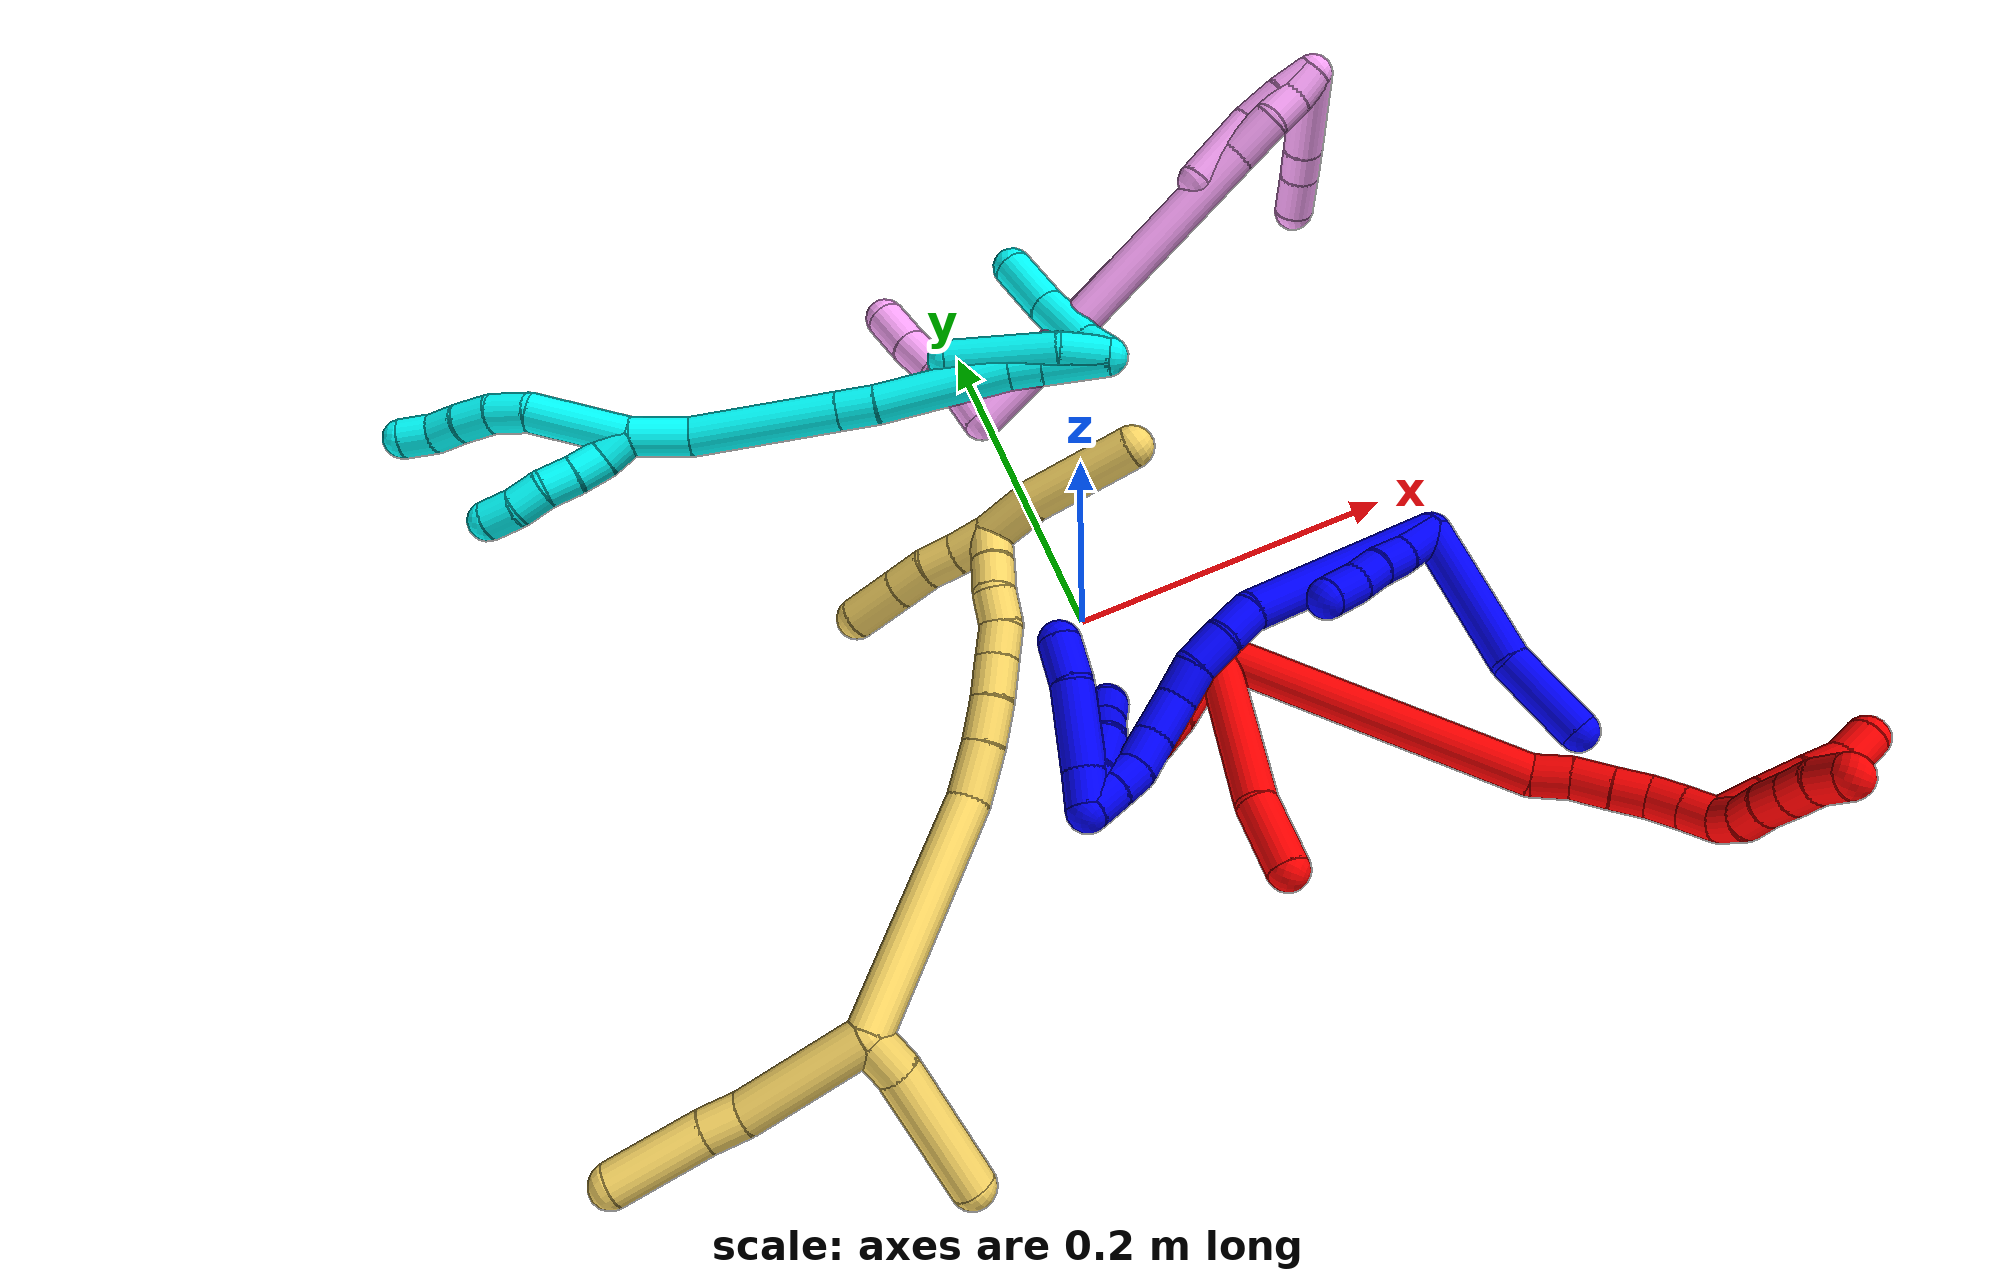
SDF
<sdf version="1.7">
 <world name="default">
  <plugin name="TubeGeneratorPlugin" filename="libtube_generator_plugin.so"/>
  <model name="photoneo_s_sensor">
   <static>1</static>
   <pose>0 0 2 1.57079 1.57079 3.14159</pose>
   <link name="link">
    <inertial><mass>0.1</mass></inertial>
    <sensor name="sensor" type="depth">
     <update_rate>30</update_rate>
     <camera>
      <horizontal_fov>1.22</horizontal_fov>
      <image><width>1920</width><height>1200</height><format>B8G8R8</format></image>
      <clip><near>0.1</near><far>4</far></clip>
      <depth_camera><output>points</output></depth_camera>
     </camera>
     <plugin name="camera_plugin" filename="libgazebo_ros_depth_camera.so">
      <baseline>0.2</baseline>
      <alwaysOn>1</alwaysOn>
      <updateRate>0.0</updateRate>
      <cameraName>camera_ir</cameraName>
      <imageTopicName>/camera/color/image_raw</imageTopicName>
      <cameraInfoTopicName>/camera/color/camera_info</cameraInfoTopicName>
      <depthImageTopicName>/camera/depth/image_raw</depthImageTopicName>
      <depthImageCameraInfoTopicName>/camera/depth/camera_info</depthImageCameraInfoTopicName>
      <pointCloudTopicName>/camera/depth/points</pointCloudTopicName>
      <frameName>fr_optical</frameName>
      <pointCloudCutoff>0.1</pointCloudCutoff>
      <pointCloudCutoffMax>2.0</pointCloudCutoffMax>
      <distortionK1>0</distortionK1>
      <distortionK2>0</distortionK2>
      <distortionK3>0</distortionK3>
      <distortionT1>0</distortionT1>
      <distortionT2>0</distortionT2>
      <CxPrime>0</CxPrime>
      <Cx>0</Cx>
      <Cy>0</Cy>
      <focalLength>0</focalLength>
      <hackBaseline>0</hackBaseline>
     </plugin>
    </sensor>
   </link>
  </model>
  <gravity>0 0 -9.8</gravity>
  <magnetic_field>6e-06 2.3e-05 -4.2e-05</magnetic_field>
  <atmosphere type="adiabatic"/>
  <physics name="default_physics" default="0" type="ode">
   <max_step_size>0.003</max_step_size>
   <real_time_factor>1</real_time_factor>
   <real_time_update_rate>1000</real_time_update_rate>
   <max_contacts>10000</max_contacts>
   <ode>
    <solver>
     <type>quick</type>
     <iters>100</iters>
     <sor>1.3</sor>
     <use_dynamic_moi_rescaling>0</use_dynamic_moi_rescaling>
    </solver>
    <constraints>
     <contact_max_correcting_vel>0</contact_max_correcting_vel>
     <contact_surface_layer>0.001</contact_surface_layer>
     <cfm>0</cfm>
     <erp>0.2</erp>
    </constraints>
   </ode>
  </physics>
  <scene><ambient>0.4 0.4 0.4 1</ambient><background>0.7 0.7 0.7 1</background><shadows>0</shadows></scene>
  <audio><device>default</device></audio>
  <spherical_coordinates>
   <surface_model>EARTH_WGS84</surface_model>
   <latitude_deg>0</latitude_deg>
   <longitude_deg>0</longitude_deg>
   <elevation>0</elevation>
   <heading_deg>0</heading_deg>
  </spherical_coordinates>
  <model name="bin">
   <static>1</static>
   <link name="bottom">
    <collision name="collision-bottom">
     <pose>0 0 -0.01 0 -0 0</pose>
     <geometry><box><size>0.8 0.6 0.02</size></box></geometry>
     <surface>
      <friction><ode><mu>100</mu><mu2>100</mu2></ode></friction>
      <contact><collide_bitmask>65535</collide_bitmask></contact>
     </surface>
    </collision>
   </link>
   <link name="west_wall">
    <collision name="collision-west_wall">
     <pose>-0.41 0 0.1 0 -0 0</pose>
     <geometry><box><size>0.02 0.6 0.2</size></box></geometry>
     <surface>
      <friction><ode><mu>100</mu><mu2>100</mu2></ode></friction>
      <contact><collide_bitmask>65535</collide_bitmask></contact>
     </surface>
    </collision>
   </link>
   <link name="east_wall">
    <collision name="collision-east_wall">
     <pose>0.41 0 0.1 0 -0 0</pose>
     <geometry><box><size>0.02 0.6 0.2</size></box></geometry>
     <surface>
      <friction><ode><mu>100</mu><mu2>100</mu2></ode></friction>
      <contact><collide_bitmask>65535</collide_bitmask></contact>
     </surface>
    </collision>
   </link>
   <link name="south_wall">
    <collision name="collision-south_wall">
     <pose>0 -0.31 0.1 0 -0 0</pose>
     <geometry><box><size>0.8 0.02 0.2</size></box></geometry>
     <surface>
      <friction><ode><mu>100</mu><mu2>100</mu2></ode></friction>
      <contact><collide_bitmask>65535</collide_bitmask></contact>
     </surface>
    </collision>
   </link>
   <link name="north_wall">
    <collision name="collision-north_wall">
     <pose>0 0.31 0.1 0 -0 0</pose>
     <geometry><box><size>0.8 0.02 0.2</size></box></geometry>
     <surface>
      <friction><ode><mu>100</mu><mu2>100</mu2></ode></friction>
      <contact><collide_bitmask>65535</collide_bitmask></contact>
     </surface>
    </collision>
   </link>
  </model>
  <model name="1">
   <static>0</static>
   <link name="1">
    <collision name="collision-cylinder-e_1_2_8">
     <pose>-0.005855 -0.023077 0.040562 0.517259 -0.124804 -0.033058</pose>
     <geometry><cylinder><radius>0.0125</radius><length>0.094065</length></cylinder></geometry>
     <surface>
      <friction><ode><mu>1.16</mu><mu2>1.16</mu2><slip1>0</slip1><slip2>0</slip2></ode></friction>
      <contact><ode><kp>1e+06</kp><kd>1</kd><max_vel>0</max_vel><min_depth>0.001</min_depth></ode></contact>
     </surface>
    </collision>
    <visual name="visual-cylinder-e_1_2_8">
     <pose>-0.005855 -0.023077 0.040562 0.517259 -0.124804 -0.033058</pose>
     <geometry><cylinder><radius>0.0125</radius><length>0.094065</length></cylinder></geometry>
     <material><ambient>0 0 1 1</ambient></material>
    </visual>
    <collision name="collision-cylinder-e_2_8_6">
     <pose>-0.007784 -0.058919 0.105696 0.479143 0.140809 0.034448</pose>
     <geometry><cylinder><radius>0.0125</radius><length>0.055935</length></cylinder></geometry>
     <surface>
      <friction><ode><mu>1.16</mu><mu2>1.16</mu2><slip1>0</slip1><slip2>0</slip2></ode></friction>
      <contact><ode><kp>1e+06</kp><kd>1</kd><max_vel>0</max_vel><min_depth>0.001</min_depth></ode></contact>
     </surface>
    </collision>
    <visual name="visual-cylinder-e_2_8_6">
     <pose>-0.007784 -0.058919 0.105696 0.479143 0.140809 0.034448</pose>
     <geometry><cylinder><radius>0.0125</radius><length>0.055935</length></cylinder></geometry>
     <material><ambient>0 0 1 1</ambient></material>
    </visual>
    <collision name="collision-cylinder-e_1_2_9">
     <pose>-0.015929 -0.001294 0.002911 0.418196 -1.37342 -0.344483</pose>
     <geometry><cylinder><radius>0.0125</radius><length>0.032488</length></cylinder></geometry>
     <surface>
      <friction><ode><mu>1.16</mu><mu2>1.16</mu2><slip1>0</slip1><slip2>0</slip2></ode></friction>
      <contact><ode><kp>1e+06</kp><kd>1</kd><max_vel>0</max_vel><min_depth>0.001</min_depth></ode></contact>
     </surface>
    </collision>
    <visual name="visual-cylinder-e_1_2_9">
     <pose>-0.015929 -0.001294 0.002911 0.418196 -1.37342 -0.344483</pose>
     <geometry><cylinder><radius>0.0125</radius><length>0.032488</length></cylinder></geometry>
     <material><ambient>0 0 1 1</ambient></material>
    </visual>
    <collision name="collision-cylinder-e_2_9_10">
     <pose>-0.043145 -0.002468 0.007033 -0.097905 -1.46338 0.087928</pose>
     <geometry><cylinder><radius>0.0125</radius><length>0.022705</length></cylinder></geometry>
     <surface>
      <friction><ode><mu>1.16</mu><mu2>1.16</mu2><slip1>0</slip1><slip2>0</slip2></ode></friction>
      <contact><ode><kp>1e+06</kp><kd>1</kd><max_vel>0</max_vel><min_depth>0.001</min_depth></ode></contact>
     </surface>
    </collision>
    <visual name="visual-cylinder-e_2_9_10">
     <pose>-0.043145 -0.002468 0.007033 -0.097905 -1.46338 0.087928</pose>
     <geometry><cylinder><radius>0.0125</radius><length>0.022705</length></cylinder></geometry>
     <material><ambient>0 0 1 1</ambient></material>
    </visual>
    <collision name="collision-cylinder-e_3_10_11">
     <pose>-0.064322 -0.003582 0.009586 0.743216 -1.38866 -0.627545</pose>
     <geometry><cylinder><radius>0.0125</radius><length>0.020113</length></cylinder></geometry>
     <surface>
      <friction><ode><mu>1.16</mu><mu2>1.16</mu2><slip1>0</slip1><slip2>0</slip2></ode></friction>
      <contact><ode><kp>1e+06</kp><kd>1</kd><max_vel>0</max_vel><min_depth>0.001</min_depth></ode></contact>
     </surface>
    </collision>
    <visual name="visual-cylinder-e_3_10_11">
     <pose>-0.064322 -0.003582 0.009586 0.743216 -1.38866 -0.627545</pose>
     <geometry><cylinder><radius>0.0125</radius><length>0.020113</length></cylinder></geometry>
     <material><ambient>0 0 1 1</ambient></material>
    </visual>
    <collision name="collision-cylinder-e_4_11_5">
     <pose>-0.08649 -0.004771 0.012231 -0.032967 -1.46493 0.02965</pose>
     <geometry><cylinder><radius>0.0125</radius><length>0.024694</length></cylinder></geometry>
     <surface>
      <friction><ode><mu>1.16</mu><mu2>1.16</mu2><slip1>0</slip1><slip2>0</slip2></ode></friction>
      <contact><ode><kp>1e+06</kp><kd>1</kd><max_vel>0</max_vel><min_depth>0.001</min_depth></ode></contact>
     </surface>
    </collision>
    <visual name="visual-cylinder-e_4_11_5">
     <pose>-0.08649 -0.004771 0.012231 -0.032967 -1.46493 0.02965</pose>
     <geometry><cylinder><radius>0.0125</radius><length>0.024694</length></cylinder></geometry>
     <material><ambient>0 0 1 1</ambient></material>
    </visual>
    <collision name="collision-cylinder-e_1_2_12">
     <pose>-0.069825 -0.004302 -0.003206 2.21114 -1.49411 -2.14819</pose>
     <geometry><cylinder><radius>0.0125</radius><length>0.140061</length></cylinder></geometry>
     <surface>
      <friction><ode><mu>1.16</mu><mu2>1.16</mu2><slip1>0</slip1><slip2>0</slip2></ode></friction>
      <contact><ode><kp>1e+06</kp><kd>1</kd><max_vel>0</max_vel><min_depth>0.001</min_depth></ode></contact>
     </surface>
    </collision>
    <visual name="visual-cylinder-e_1_2_12">
     <pose>-0.069825 -0.004302 -0.003206 2.21114 -1.49411 -2.14819</pose>
     <geometry><cylinder><radius>0.0125</radius><length>0.140061</length></cylinder></geometry>
     <material><ambient>0 0 1 1</ambient></material>
    </visual>
    <collision name="collision-cylinder-e_2_12_13">
     <pose>-0.150979 -0.012207 -0.004788 1.14728 -1.23527 -0.860564</pose>
     <geometry><cylinder><radius>0.0125</radius><length>0.023998</length></cylinder></geometry>
     <surface>
      <friction><ode><mu>1.16</mu><mu2>1.16</mu2><slip1>0</slip1><slip2>0</slip2></ode></friction>
      <contact><ode><kp>1e+06</kp><kd>1</kd><max_vel>0</max_vel><min_depth>0.001</min_depth></ode></contact>
     </surface>
    </collision>
    <visual name="visual-cylinder-e_2_12_13">
     <pose>-0.150979 -0.012207 -0.004788 1.14728 -1.23527 -0.860564</pose>
     <geometry><cylinder><radius>0.0125</radius><length>0.023998</length></cylinder></geometry>
     <material><ambient>0 0 1 1</ambient></material>
    </visual>
    <collision name="collision-cylinder-e_3_13_14">
     <pose>-0.172808 -0.02137 -0.002815 1.50813 -1.08285 -1.02829</pose>
     <geometry><cylinder><radius>0.0125</radius><length>0.023774</length></cylinder></geometry>
     <surface>
      <friction><ode><mu>1.16</mu><mu2>1.16</mu2><slip1>0</slip1><slip2>0</slip2></ode></friction>
      <contact><ode><kp>1e+06</kp><kd>1</kd><max_vel>0</max_vel><min_depth>0.001</min_depth></ode></contact>
     </surface>
    </collision>
    <visual name="visual-cylinder-e_3_13_14">
     <pose>-0.172808 -0.02137 -0.002815 1.50813 -1.08285 -1.02829</pose>
     <geometry><cylinder><radius>0.0125</radius><length>0.023774</length></cylinder></geometry>
     <material><ambient>0 0 1 1</ambient></material>
    </visual>
    <collision name="collision-cylinder-e_4_14_15">
     <pose>-0.191263 -0.034244 -0.00081 1.34803 -0.815026 -0.664117</pose>
     <geometry><cylinder><radius>0.0125</radius><length>0.021862</length></cylinder></geometry>
     <surface>
      <friction><ode><mu>1.16</mu><mu2>1.16</mu2><slip1>0</slip1><slip2>0</slip2></ode></friction>
      <contact><ode><kp>1e+06</kp><kd>1</kd><max_vel>0</max_vel><min_depth>0.001</min_depth></ode></contact>
     </surface>
    </collision>
    <visual name="visual-cylinder-e_4_14_15">
     <pose>-0.191263 -0.034244 -0.00081 1.34803 -0.815026 -0.664117</pose>
     <geometry><cylinder><radius>0.0125</radius><length>0.021862</length></cylinder></geometry>
     <material><ambient>0 0 1 1</ambient></material>
    </visual>
    <collision name="collision-cylinder-e_5_15_16">
     <pose>-0.210727 -0.047723 0.005063 0.971184 -0.99504 -0.558252</pose>
     <geometry><cylinder><radius>0.0125</radius><length>0.027442</length></cylinder></geometry>
     <surface>
      <friction><ode><mu>1.16</mu><mu2>1.16</mu2><slip1>0</slip1><slip2>0</slip2></ode></friction>
      <contact><ode><kp>1e+06</kp><kd>1</kd><max_vel>0</max_vel><min_depth>0.001</min_depth></ode></contact>
     </surface>
    </collision>
    <visual name="visual-cylinder-e_5_15_16">
     <pose>-0.210727 -0.047723 0.005063 0.971184 -0.99504 -0.558252</pose>
     <geometry><cylinder><radius>0.0125</radius><length>0.027442</length></cylinder></geometry>
     <material><ambient>0 0 1 1</ambient></material>
    </visual>
    <collision name="collision-cylinder-e_6_16_17">
     <pose>-0.231712 -0.0581 0.013334 0.804007 -1.01815 -0.465977</pose>
     <geometry><cylinder><radius>0.0125</radius><length>0.022268</length></cylinder></geometry>
     <surface>
      <friction><ode><mu>1.16</mu><mu2>1.16</mu2><slip1>0</slip1><slip2>0</slip2></ode></friction>
      <contact><ode><kp>1e+06</kp><kd>1</kd><max_vel>0</max_vel><min_depth>0.001</min_depth></ode></contact>
     </surface>
    </collision>
    <visual name="visual-cylinder-e_6_16_17">
     <pose>-0.231712 -0.0581 0.013334 0.804007 -1.01815 -0.465977</pose>
     <geometry><cylinder><radius>0.0125</radius><length>0.022268</length></cylinder></geometry>
     <material><ambient>0 0 1 1</ambient></material>
    </visual>
    <collision name="collision-cylinder-e_7_17_18">
     <pose>-0.250867 -0.063141 0.019836 0.327763 -1.30979 -0.252633</pose>
     <geometry><cylinder><radius>0.0125</radius><length>0.020035</length></cylinder></geometry>
     <surface>
      <friction><ode><mu>1.16</mu><mu2>1.16</mu2><slip1>0</slip1><slip2>0</slip2></ode></friction>
      <contact><ode><kp>1e+06</kp><kd>1</kd><max_vel>0</max_vel><min_depth>0.001</min_depth></ode></contact>
     </surface>
    </collision>
    <visual name="visual-cylinder-e_7_17_18">
     <pose>-0.250867 -0.063141 0.019836 0.327763 -1.30979 -0.252633</pose>
     <geometry><cylinder><radius>0.0125</radius><length>0.020035</length></cylinder></geometry>
     <material><ambient>0 0 1 1</ambient></material>
    </visual>
    <collision name="collision-cylinder-e_8_18_1">
     <pose>-0.270532 -0.064876 0.02455 0.37934 -1.33121 -0.299201</pose>
     <geometry><cylinder><radius>0.0125</radius><length>0.020561</length></cylinder></geometry>
     <surface>
      <friction><ode><mu>1.16</mu><mu2>1.16</mu2><slip1>0</slip1><slip2>0</slip2></ode></friction>
      <contact><ode><kp>1e+06</kp><kd>1</kd><max_vel>0</max_vel><min_depth>0.001</min_depth></ode></contact>
     </surface>
    </collision>
    <visual name="visual-cylinder-e_8_18_1">
     <pose>-0.270532 -0.064876 0.02455 0.37934 -1.33121 -0.299201</pose>
     <geometry><cylinder><radius>0.0125</radius><length>0.020561</length></cylinder></geometry>
     <material><ambient>0 0 1 1</ambient></material>
    </visual>
    <collision name="collision-cylinder-e_1_1_19">
     <pose>-0.271625 -0.062634 0.018616 -2.77533 0.79167 -2.30724</pose>
     <geometry><cylinder><radius>0.0125</radius><length>0.024999</length></cylinder></geometry>
     <surface>
      <friction><ode><mu>1.16</mu><mu2>1.16</mu2><slip1>0</slip1><slip2>0</slip2></ode></friction>
      <contact><ode><kp>1e+06</kp><kd>1</kd><max_vel>0</max_vel><min_depth>0.001</min_depth></ode></contact>
     </surface>
    </collision>
    <visual name="visual-cylinder-e_1_1_19">
     <pose>-0.271625 -0.062634 0.018616 -2.77533 0.79167 -2.30724</pose>
     <geometry><cylinder><radius>0.0125</radius><length>0.024999</length></cylinder></geometry>
     <material><ambient>0 0 1 1</ambient></material>
    </visual>
    <collision name="collision-cylinder-e_2_19_20">
     <pose>-0.251311 -0.059189 -0.000161 -3.11323 0.823541 -3.07668</pose>
     <geometry><cylinder><radius>0.0125</radius><length>0.031135</length></cylinder></geometry>
     <surface>
      <friction><ode><mu>1.16</mu><mu2>1.16</mu2><slip1>0</slip1><slip2>0</slip2></ode></friction>
      <contact><ode><kp>1e+06</kp><kd>1</kd><max_vel>0</max_vel><min_depth>0.001</min_depth></ode></contact>
     </surface>
    </collision>
    <visual name="visual-cylinder-e_2_19_20">
     <pose>-0.251311 -0.059189 -0.000161 -3.11323 0.823541 -3.07668</pose>
     <geometry><cylinder><radius>0.0125</radius><length>0.031135</length></cylinder></geometry>
     <material><ambient>0 0 1 1</ambient></material>
    </visual>
    <collision name="collision-cylinder-e_3_20_21">
     <pose>-0.233873 -0.060708 -0.019285 2.93191 0.603102 2.48913</pose>
     <geometry><cylinder><radius>0.0125</radius><length>0.021223</length></cylinder></geometry>
     <surface>
      <friction><ode><mu>1.16</mu><mu2>1.16</mu2><slip1>0</slip1><slip2>0</slip2></ode></friction>
      <contact><ode><kp>1e+06</kp><kd>1</kd><max_vel>0</max_vel><min_depth>0.001</min_depth></ode></contact>
     </surface>
    </collision>
    <visual name="visual-cylinder-e_3_20_21">
     <pose>-0.233873 -0.060708 -0.019285 2.93191 0.603102 2.48913</pose>
     <geometry><cylinder><radius>0.0125</radius><length>0.021223</length></cylinder></geometry>
     <material><ambient>0 0 1 1</ambient></material>
    </visual>
    <collision name="collision-cylinder-e_4_21_4">
     <pose>-0.220339 -0.063535 -0.03624 3.02233 0.725908 2.82973</pose>
     <geometry><cylinder><radius>0.0125</radius><length>0.022642</length></cylinder></geometry>
     <surface>
      <friction><ode><mu>1.16</mu><mu2>1.16</mu2><slip1>0</slip1><slip2>0</slip2></ode></friction>
      <contact><ode><kp>1e+06</kp><kd>1</kd><max_vel>0</max_vel><min_depth>0.001</min_depth></ode></contact>
     </surface>
    </collision>
    <visual name="visual-cylinder-e_4_21_4">
     <pose>-0.220339 -0.063535 -0.03624 3.02233 0.725908 2.82973</pose>
     <geometry><cylinder><radius>0.0125</radius><length>0.022642</length></cylinder></geometry>
     <material><ambient>0 0 1 1</ambient></material>
    </visual>
    <collision name="collision-cylinder-e_1_1_22">
     <pose>-0.275766 -0.06021 0.018592 -2.54629 0.446303 -1.27383</pose>
     <geometry><cylinder><radius>0.0125</radius><length>0.022022</length></cylinder></geometry>
     <surface>
      <friction><ode><mu>1.16</mu><mu2>1.16</mu2><slip1>0</slip1><slip2>0</slip2></ode></friction>
      <contact><ode><kp>1e+06</kp><kd>1</kd><max_vel>0</max_vel><min_depth>0.001</min_depth></ode></contact>
     </surface>
    </collision>
    <visual name="visual-cylinder-e_1_1_22">
     <pose>-0.275766 -0.06021 0.018592 -2.54629 0.446303 -1.27383</pose>
     <geometry><cylinder><radius>0.0125</radius><length>0.022022</length></cylinder></geometry>
     <material><ambient>0 0 1 1</ambient></material>
    </visual>
    <collision name="collision-cylinder-e_2_22_23">
     <pose>-0.262125 -0.038739 -0.007161 -2.40486 0.359269 -0.879478</pose>
     <geometry><cylinder><radius>0.0125</radius><length>0.050562</length></cylinder></geometry>
     <surface>
      <friction><ode><mu>1.16</mu><mu2>1.16</mu2><slip1>0</slip1><slip2>0</slip2></ode></friction>
      <contact><ode><kp>1e+06</kp><kd>1</kd><max_vel>0</max_vel><min_depth>0.001</min_depth></ode></contact>
     </surface>
    </collision>
    <visual name="visual-cylinder-e_2_22_23">
     <pose>-0.262125 -0.038739 -0.007161 -2.40486 0.359269 -0.879478</pose>
     <geometry><cylinder><radius>0.0125</radius><length>0.050562</length></cylinder></geometry>
     <material><ambient>0 0 1 1</ambient></material>
    </visual>
    <collision name="collision-cylinder-e_3_23_3">
     <pose>-0.249113 -0.016591 -0.036174 -2.64337 0.305507 -1.08842</pose>
     <geometry><cylinder><radius>0.0125</radius><length>0.027416</length></cylinder></geometry>
     <surface>
      <friction><ode><mu>1.16</mu><mu2>1.16</mu2><slip1>0</slip1><slip2>0</slip2></ode></friction>
      <contact><ode><kp>1e+06</kp><kd>1</kd><max_vel>0</max_vel><min_depth>0.001</min_depth></ode></contact>
     </surface>
    </collision>
    <visual name="visual-cylinder-e_3_23_3">
     <pose>-0.249113 -0.016591 -0.036174 -2.64337 0.305507 -1.08842</pose>
     <geometry><cylinder><radius>0.0125</radius><length>0.027416</length></cylinder></geometry>
     <material><ambient>0 0 1 1</ambient></material>
    </visual>
    <collision name="collision-sphere-3">
     <pose>-0.24499 -0.010344 -0.047658 0 -0 0</pose>
     <geometry><sphere><radius>0.0125</radius></sphere></geometry>
     <surface>
      <friction><ode><mu>1.16</mu><mu2>1.16</mu2><slip1>0</slip1><slip2>0</slip2></ode></friction>
      <contact><ode><kp>1e+06</kp><kd>1</kd><max_vel>0</max_vel><min_depth>0.001</min_depth></ode></contact>
     </surface>
    </collision>
    <visual name="visual-sphere-3">
     <pose>-0.24499 -0.010344 -0.047658 0 -0 0</pose>
     <geometry><sphere><radius>0.0125</radius></sphere></geometry>
     <material><ambient>0 0 1 1</ambient></material>
    </visual>
    <collision name="collision-sphere-23">
     <pose>-0.253236 -0.022838 -0.02469 0 -0 0</pose>
     <geometry><sphere><radius>0.0125</radius></sphere></geometry>
     <surface>
      <friction><ode><mu>1.16</mu><mu2>1.16</mu2><slip1>0</slip1><slip2>0</slip2></ode></friction>
      <contact><ode><kp>1e+06</kp><kd>1</kd><max_vel>0</max_vel><min_depth>0.001</min_depth></ode></contact>
     </surface>
    </collision>
    <visual name="visual-sphere-23">
     <pose>-0.253236 -0.022838 -0.02469 0 -0 0</pose>
     <geometry><sphere><radius>0.0125</radius></sphere></geometry>
     <material><ambient>0 0 1 1</ambient></material>
    </visual>
    <collision name="collision-sphere-22">
     <pose>-0.271013 -0.05464 0.010368 0 -0 0</pose>
     <geometry><sphere><radius>0.0125</radius></sphere></geometry>
     <surface>
      <friction><ode><mu>1.16</mu><mu2>1.16</mu2><slip1>0</slip1><slip2>0</slip2></ode></friction>
      <contact><ode><kp>1e+06</kp><kd>1</kd><max_vel>0</max_vel><min_depth>0.001</min_depth></ode></contact>
     </surface>
    </collision>
    <visual name="visual-sphere-22">
     <pose>-0.271013 -0.05464 0.010368 0 -0 0</pose>
     <geometry><sphere><radius>0.0125</radius></sphere></geometry>
     <material><ambient>0 0 1 1</ambient></material>
    </visual>
    <collision name="collision-sphere-4">
     <pose>-0.212823 -0.064542 -0.044647 0 -0 0</pose>
     <geometry><sphere><radius>0.0125</radius></sphere></geometry>
     <surface>
      <friction><ode><mu>1.16</mu><mu2>1.16</mu2><slip1>0</slip1><slip2>0</slip2></ode></friction>
      <contact><ode><kp>1e+06</kp><kd>1</kd><max_vel>0</max_vel><min_depth>0.001</min_depth></ode></contact>
     </surface>
    </collision>
    <visual name="visual-sphere-4">
     <pose>-0.212823 -0.064542 -0.044647 0 -0 0</pose>
     <geometry><sphere><radius>0.0125</radius></sphere></geometry>
     <material><ambient>0 0 1 1</ambient></material>
    </visual>
    <collision name="collision-sphere-21">
     <pose>-0.227854 -0.062527 -0.027833 0 -0 0</pose>
     <geometry><sphere><radius>0.0125</radius></sphere></geometry>
     <surface>
      <friction><ode><mu>1.16</mu><mu2>1.16</mu2><slip1>0</slip1><slip2>0</slip2></ode></friction>
      <contact><ode><kp>1e+06</kp><kd>1</kd><max_vel>0</max_vel><min_depth>0.001</min_depth></ode></contact>
     </surface>
    </collision>
    <visual name="visual-sphere-21">
     <pose>-0.227854 -0.062527 -0.027833 0 -0 0</pose>
     <geometry><sphere><radius>0.0125</radius></sphere></geometry>
     <material><ambient>0 0 1 1</ambient></material>
    </visual>
    <collision name="collision-sphere-20">
     <pose>-0.239891 -0.058889 -0.010737 0 -0 0</pose>
     <geometry><sphere><radius>0.0125</radius></sphere></geometry>
     <surface>
      <friction><ode><mu>1.16</mu><mu2>1.16</mu2><slip1>0</slip1><slip2>0</slip2></ode></friction>
      <contact><ode><kp>1e+06</kp><kd>1</kd><max_vel>0</max_vel><min_depth>0.001</min_depth></ode></contact>
     </surface>
    </collision>
    <visual name="visual-sphere-20">
     <pose>-0.239891 -0.058889 -0.010737 0 -0 0</pose>
     <geometry><sphere><radius>0.0125</radius></sphere></geometry>
     <material><ambient>0 0 1 1</ambient></material>
    </visual>
    <collision name="collision-sphere-11">
     <pose>-0.074212 -0.004814 0.010927 0 -0 0</pose>
     <geometry><sphere><radius>0.0125</radius></sphere></geometry>
     <surface>
      <friction><ode><mu>1.16</mu><mu2>1.16</mu2><slip1>0</slip1><slip2>0</slip2></ode></friction>
      <contact><ode><kp>1e+06</kp><kd>1</kd><max_vel>0</max_vel><min_depth>0.001</min_depth></ode></contact>
     </surface>
    </collision>
    <visual name="visual-sphere-11">
     <pose>-0.074212 -0.004814 0.010927 0 -0 0</pose>
     <geometry><sphere><radius>0.0125</radius></sphere></geometry>
     <material><ambient>0 0 1 1</ambient></material>
    </visual>
    <collision name="collision-sphere-10">
     <pose>-0.054432 -0.002349 0.008245 0 -0 0</pose>
     <geometry><sphere><radius>0.0125</radius></sphere></geometry>
     <surface>
      <friction><ode><mu>1.16</mu><mu2>1.16</mu2><slip1>0</slip1><slip2>0</slip2></ode></friction>
      <contact><ode><kp>1e+06</kp><kd>1</kd><max_vel>0</max_vel><min_depth>0.001</min_depth></ode></contact>
     </surface>
    </collision>
    <visual name="visual-sphere-10">
     <pose>-0.054432 -0.002349 0.008245 0 -0 0</pose>
     <geometry><sphere><radius>0.0125</radius></sphere></geometry>
     <material><ambient>0 0 1 1</ambient></material>
    </visual>
    <collision name="collision-sphere-6">
     <pose>-0.003859 -0.071685 0.130268 0 -0 0</pose>
     <geometry><sphere><radius>0.0125</radius></sphere></geometry>
     <surface>
      <friction><ode><mu>1.16</mu><mu2>1.16</mu2><slip1>0</slip1><slip2>0</slip2></ode></friction>
      <contact><ode><kp>1e+06</kp><kd>1</kd><max_vel>0</max_vel><min_depth>0.001</min_depth></ode></contact>
     </surface>
    </collision>
    <visual name="visual-sphere-6">
     <pose>-0.003859 -0.071685 0.130268 0 -0 0</pose>
     <geometry><sphere><radius>0.0125</radius></sphere></geometry>
     <material><ambient>0 0 1 1</ambient></material>
    </visual>
    <collision name="collision-sphere-9">
     <pose>-0.031858 -0.002587 0.005822 0 -0 0</pose>
     <geometry><sphere><radius>0.0125</radius></sphere></geometry>
     <surface>
      <friction><ode><mu>1.16</mu><mu2>1.16</mu2><slip1>0</slip1><slip2>0</slip2></ode></friction>
      <contact><ode><kp>1e+06</kp><kd>1</kd><max_vel>0</max_vel><min_depth>0.001</min_depth></ode></contact>
     </surface>
    </collision>
    <visual name="visual-sphere-9">
     <pose>-0.031858 -0.002587 0.005822 0 -0 0</pose>
     <geometry><sphere><radius>0.0125</radius></sphere></geometry>
     <material><ambient>0 0 1 1</ambient></material>
    </visual>
    <collision name="collision-sphere-2">
     <geometry><sphere><radius>0.0125</radius></sphere></geometry>
     <surface>
      <friction><ode><mu>1.16</mu><mu2>1.16</mu2><slip1>0</slip1><slip2>0</slip2></ode></friction>
      <contact><ode><kp>1e+06</kp><kd>1</kd><max_vel>0</max_vel><min_depth>0.001</min_depth></ode></contact>
     </surface>
    </collision>
    <visual name="visual-sphere-2">
     <geometry><sphere><radius>0.0125</radius></sphere></geometry>
     <material><ambient>0 0 1 1</ambient></material>
    </visual>
    <collision name="collision-sphere-19">
     <pose>-0.262731 -0.059489 0.010415 0 -0 0</pose>
     <geometry><sphere><radius>0.0125</radius></sphere></geometry>
     <surface>
      <friction><ode><mu>1.16</mu><mu2>1.16</mu2><slip1>0</slip1><slip2>0</slip2></ode></friction>
      <contact><ode><kp>1e+06</kp><kd>1</kd><max_vel>0</max_vel><min_depth>0.001</min_depth></ode></contact>
     </surface>
    </collision>
    <visual name="visual-sphere-19">
     <pose>-0.262731 -0.059489 0.010415 0 -0 0</pose>
     <geometry><sphere><radius>0.0125</radius></sphere></geometry>
     <material><ambient>0 0 1 1</ambient></material>
    </visual>
    <collision name="collision-sphere-8">
     <pose>-0.011709 -0.046153 0.081123 0 -0 0</pose>
     <geometry><sphere><radius>0.0125</radius></sphere></geometry>
     <surface>
      <friction><ode><mu>1.16</mu><mu2>1.16</mu2><slip1>0</slip1><slip2>0</slip2></ode></friction>
      <contact><ode><kp>1e+06</kp><kd>1</kd><max_vel>0</max_vel><min_depth>0.001</min_depth></ode></contact>
     </surface>
    </collision>
    <visual name="visual-sphere-8">
     <pose>-0.011709 -0.046153 0.081123 0 -0 0</pose>
     <geometry><sphere><radius>0.0125</radius></sphere></geometry>
     <material><ambient>0 0 1 1</ambient></material>
    </visual>
    <collision name="collision-sphere-5">
     <pose>-0.098767 -0.004728 0.013535 0 -0 0</pose>
     <geometry><sphere><radius>0.0125</radius></sphere></geometry>
     <surface>
      <friction><ode><mu>1.16</mu><mu2>1.16</mu2><slip1>0</slip1><slip2>0</slip2></ode></friction>
      <contact><ode><kp>1e+06</kp><kd>1</kd><max_vel>0</max_vel><min_depth>0.001</min_depth></ode></contact>
     </surface>
    </collision>
    <visual name="visual-sphere-5">
     <pose>-0.098767 -0.004728 0.013535 0 -0 0</pose>
     <geometry><sphere><radius>0.0125</radius></sphere></geometry>
     <material><ambient>0 0 1 1</ambient></material>
    </visual>
    <collision name="collision-sphere-12">
     <pose>-0.139649 -0.008605 -0.006411 0 -0 0</pose>
     <geometry><sphere><radius>0.0125</radius></sphere></geometry>
     <surface>
      <friction><ode><mu>1.16</mu><mu2>1.16</mu2><slip1>0</slip1><slip2>0</slip2></ode></friction>
      <contact><ode><kp>1e+06</kp><kd>1</kd><max_vel>0</max_vel><min_depth>0.001</min_depth></ode></contact>
     </surface>
    </collision>
    <visual name="visual-sphere-12">
     <pose>-0.139649 -0.008605 -0.006411 0 -0 0</pose>
     <geometry><sphere><radius>0.0125</radius></sphere></geometry>
     <material><ambient>0 0 1 1</ambient></material>
    </visual>
    <collision name="collision-sphere-13">
     <pose>-0.162309 -0.015808 -0.003164 0 -0 0</pose>
     <geometry><sphere><radius>0.0125</radius></sphere></geometry>
     <surface>
      <friction><ode><mu>1.16</mu><mu2>1.16</mu2><slip1>0</slip1><slip2>0</slip2></ode></friction>
      <contact><ode><kp>1e+06</kp><kd>1</kd><max_vel>0</max_vel><min_depth>0.001</min_depth></ode></contact>
     </surface>
    </collision>
    <visual name="visual-sphere-13">
     <pose>-0.162309 -0.015808 -0.003164 0 -0 0</pose>
     <geometry><sphere><radius>0.0125</radius></sphere></geometry>
     <material><ambient>0 0 1 1</ambient></material>
    </visual>
    <collision name="collision-sphere-14">
     <pose>-0.183308 -0.026932 -0.002466 0 -0 0</pose>
     <geometry><sphere><radius>0.0125</radius></sphere></geometry>
     <surface>
      <friction><ode><mu>1.16</mu><mu2>1.16</mu2><slip1>0</slip1><slip2>0</slip2></ode></friction>
      <contact><ode><kp>1e+06</kp><kd>1</kd><max_vel>0</max_vel><min_depth>0.001</min_depth></ode></contact>
     </surface>
    </collision>
    <visual name="visual-sphere-14">
     <pose>-0.183308 -0.026932 -0.002466 0 -0 0</pose>
     <geometry><sphere><radius>0.0125</radius></sphere></geometry>
     <material><ambient>0 0 1 1</ambient></material>
    </visual>
    <collision name="collision-sphere-15">
     <pose>-0.199218 -0.041556 0.000847 0 -0 0</pose>
     <geometry><sphere><radius>0.0125</radius></sphere></geometry>
     <surface>
      <friction><ode><mu>1.16</mu><mu2>1.16</mu2><slip1>0</slip1><slip2>0</slip2></ode></friction>
      <contact><ode><kp>1e+06</kp><kd>1</kd><max_vel>0</max_vel><min_depth>0.001</min_depth></ode></contact>
     </surface>
    </collision>
    <visual name="visual-sphere-15">
     <pose>-0.199218 -0.041556 0.000847 0 -0 0</pose>
     <geometry><sphere><radius>0.0125</radius></sphere></geometry>
     <material><ambient>0 0 1 1</ambient></material>
    </visual>
    <collision name="collision-sphere-16">
     <pose>-0.222236 -0.053891 0.009278 0 -0 0</pose>
     <geometry><sphere><radius>0.0125</radius></sphere></geometry>
     <surface>
      <friction><ode><mu>1.16</mu><mu2>1.16</mu2><slip1>0</slip1><slip2>0</slip2></ode></friction>
      <contact><ode><kp>1e+06</kp><kd>1</kd><max_vel>0</max_vel><min_depth>0.001</min_depth></ode></contact>
     </surface>
    </collision>
    <visual name="visual-sphere-16">
     <pose>-0.222236 -0.053891 0.009278 0 -0 0</pose>
     <geometry><sphere><radius>0.0125</radius></sphere></geometry>
     <material><ambient>0 0 1 1</ambient></material>
    </visual>
    <collision name="collision-sphere-17">
     <pose>-0.241189 -0.062309 0.017389 0 -0 0</pose>
     <geometry><sphere><radius>0.0125</radius></sphere></geometry>
     <surface>
      <friction><ode><mu>1.16</mu><mu2>1.16</mu2><slip1>0</slip1><slip2>0</slip2></ode></friction>
      <contact><ode><kp>1e+06</kp><kd>1</kd><max_vel>0</max_vel><min_depth>0.001</min_depth></ode></contact>
     </surface>
    </collision>
    <visual name="visual-sphere-17">
     <pose>-0.241189 -0.062309 0.017389 0 -0 0</pose>
     <geometry><sphere><radius>0.0125</radius></sphere></geometry>
     <material><ambient>0 0 1 1</ambient></material>
    </visual>
    <collision name="collision-sphere-18">
     <pose>-0.260545 -0.063973 0.022284 0 -0 0</pose>
     <geometry><sphere><radius>0.0125</radius></sphere></geometry>
     <surface>
      <friction><ode><mu>1.16</mu><mu2>1.16</mu2><slip1>0</slip1><slip2>0</slip2></ode></friction>
      <contact><ode><kp>1e+06</kp><kd>1</kd><max_vel>0</max_vel><min_depth>0.001</min_depth></ode></contact>
     </surface>
    </collision>
    <visual name="visual-sphere-18">
     <pose>-0.260545 -0.063973 0.022284 0 -0 0</pose>
     <geometry><sphere><radius>0.0125</radius></sphere></geometry>
     <material><ambient>0 0 1 1</ambient></material>
    </visual>
    <collision name="collision-sphere-1">
     <pose>-0.280519 -0.06578 0.026816 0 -0 0</pose>
     <geometry><sphere><radius>0.0125</radius></sphere></geometry>
     <surface>
      <friction><ode><mu>1.16</mu><mu2>1.16</mu2><slip1>0</slip1><slip2>0</slip2></ode></friction>
      <contact><ode><kp>1e+06</kp><kd>1</kd><max_vel>0</max_vel><min_depth>0.001</min_depth></ode></contact>
     </surface>
    </collision>
    <visual name="visual-sphere-1">
     <pose>-0.280519 -0.06578 0.026816 0 -0 0</pose>
     <geometry><sphere><radius>0.0125</radius></sphere></geometry>
     <material><ambient>0 0 1 1</ambient></material>
    </visual>
    <inertial>
     <pose>-0.133146 -0.030645 0.012603 0 -0 0</pose>
     <mass>0.75</mass>
     <inertia>
      <ixx>3.3e-05</ixx>
      <ixy>0</ixy>
      <ixz>0</ixz>
      <iyy>0.000297</iyy>
      <iyz>0</iyz>
      <izz>0.000304</izz>
     </inertia>
    </inertial>
   </link>
   <pose>0.21585 -0.035345 0.011497 1.07076 0.351486 0.13934</pose>
  </model>
  <model name="2">
   <static>0</static>
   <link name="2">
    <collision name="collision-cylinder-e_1_2_8">
     <pose>-0.024674 0.037066 0.03026 -0.886148 -0.476095 0.229283</pose>
     <geometry><cylinder><radius>0.0125</radius><length>0.107674</length></cylinder></geometry>
     <surface>
      <friction><ode><mu>1.16</mu><mu2>1.16</mu2><slip1>0</slip1><slip2>0</slip2></ode></friction>
      <contact><ode><kp>1e+06</kp><kd>1</kd><max_vel>0</max_vel><min_depth>0.001</min_depth></ode></contact>
     </surface>
    </collision>
    <visual name="visual-cylinder-e_1_2_8">
     <pose>-0.024674 0.037066 0.03026 -0.886148 -0.476095 0.229283</pose>
     <geometry><cylinder><radius>0.0125</radius><length>0.107674</length></cylinder></geometry>
     <material><ambient>1 0 0 1</ambient></material>
    </visual>
    <collision name="collision-cylinder-e_2_8_6">
     <pose>-0.059328 0.085069 0.075643 -0.626105 -0.491075 0.161878</pose>
     <geometry><cylinder><radius>0.0125</radius><length>0.042326</length></cylinder></geometry>
     <surface>
      <friction><ode><mu>1.16</mu><mu2>1.16</mu2><slip1>0</slip1><slip2>0</slip2></ode></friction>
      <contact><ode><kp>1e+06</kp><kd>1</kd><max_vel>0</max_vel><min_depth>0.001</min_depth></ode></contact>
     </surface>
    </collision>
    <visual name="visual-cylinder-e_2_8_6">
     <pose>-0.059328 0.085069 0.075643 -0.626105 -0.491075 0.161878</pose>
     <geometry><cylinder><radius>0.0125</radius><length>0.042326</length></cylinder></geometry>
     <material><ambient>1 0 0 1</ambient></material>
    </visual>
    <collision name="collision-cylinder-e_1_2_9">
     <pose>-0.017497 0.016267 -0.002569 -1.72741 -0.81567 0.936298</pose>
     <geometry><cylinder><radius>0.0125</radius><length>0.048056</length></cylinder></geometry>
     <surface>
      <friction><ode><mu>1.16</mu><mu2>1.16</mu2><slip1>0</slip1><slip2>0</slip2></ode></friction>
      <contact><ode><kp>1e+06</kp><kd>1</kd><max_vel>0</max_vel><min_depth>0.001</min_depth></ode></contact>
     </surface>
    </collision>
    <visual name="visual-cylinder-e_1_2_9">
     <pose>-0.017497 0.016267 -0.002569 -1.72741 -0.81567 0.936298</pose>
     <geometry><cylinder><radius>0.0125</radius><length>0.048056</length></cylinder></geometry>
     <material><ambient>1 0 0 1</ambient></material>
    </visual>
    <collision name="collision-cylinder-e_2_9_10">
     <pose>-0.042562 0.039907 -0.007619 -1.89542 -0.771613 1.02892</pose>
     <geometry><cylinder><radius>0.0125</radius><length>0.021707</length></cylinder></geometry>
     <surface>
      <friction><ode><mu>1.16</mu><mu2>1.16</mu2><slip1>0</slip1><slip2>0</slip2></ode></friction>
      <contact><ode><kp>1e+06</kp><kd>1</kd><max_vel>0</max_vel><min_depth>0.001</min_depth></ode></contact>
     </surface>
    </collision>
    <visual name="visual-cylinder-e_2_9_10">
     <pose>-0.042562 0.039907 -0.007619 -1.89542 -0.771613 1.02892</pose>
     <geometry><cylinder><radius>0.0125</radius><length>0.021707</length></cylinder></geometry>
     <material><ambient>1 0 0 1</ambient></material>
    </visual>
    <collision name="collision-cylinder-e_3_10_5">
     <pose>-0.062295 0.054394 -0.015575 -2.22672 -0.935086 1.5961</pose>
     <geometry><cylinder><radius>0.0125</radius><length>0.030237</length></cylinder></geometry>
     <surface>
      <friction><ode><mu>1.16</mu><mu2>1.16</mu2><slip1>0</slip1><slip2>0</slip2></ode></friction>
      <contact><ode><kp>1e+06</kp><kd>1</kd><max_vel>0</max_vel><min_depth>0.001</min_depth></ode></contact>
     </surface>
    </collision>
    <visual name="visual-cylinder-e_3_10_5">
     <pose>-0.062295 0.054394 -0.015575 -2.22672 -0.935086 1.5961</pose>
     <geometry><cylinder><radius>0.0125</radius><length>0.030237</length></cylinder></geometry>
     <material><ambient>1 0 0 1</ambient></material>
    </visual>
    <collision name="collision-cylinder-e_1_2_11">
     <pose>-0.002708 -0.007805 0.096281 0.080889 -0.028029 -0.001134</pose>
     <geometry><cylinder><radius>0.0125</radius><length>0.19327</length></cylinder></geometry>
     <surface>
      <friction><ode><mu>1.16</mu><mu2>1.16</mu2><slip1>0</slip1><slip2>0</slip2></ode></friction>
      <contact><ode><kp>1e+06</kp><kd>1</kd><max_vel>0</max_vel><min_depth>0.001</min_depth></ode></contact>
     </surface>
    </collision>
    <visual name="visual-cylinder-e_1_2_11">
     <pose>-0.002708 -0.007805 0.096281 0.080889 -0.028029 -0.001134</pose>
     <geometry><cylinder><radius>0.0125</radius><length>0.19327</length></cylinder></geometry>
     <material><ambient>1 0 0 1</ambient></material>
    </visual>
    <collision name="collision-cylinder-e_2_11_12">
     <pose>-0.00189 -0.0163 0.203449 0.063229 0.312665 0.009969</pose>
     <geometry><cylinder><radius>0.0125</radius><length>0.02293</length></cylinder></geometry>
     <surface>
      <friction><ode><mu>1.16</mu><mu2>1.16</mu2><slip1>0</slip1><slip2>0</slip2></ode></friction>
      <contact><ode><kp>1e+06</kp><kd>1</kd><max_vel>0</max_vel><min_depth>0.001</min_depth></ode></contact>
     </surface>
    </collision>
    <visual name="visual-cylinder-e_2_11_12">
     <pose>-0.00189 -0.0163 0.203449 0.063229 0.312665 0.009969</pose>
     <geometry><cylinder><radius>0.0125</radius><length>0.02293</length></cylinder></geometry>
     <material><ambient>1 0 0 1</ambient></material>
    </visual>
    <collision name="collision-cylinder-e_3_12_13">
     <pose>0.003575 -0.01538 0.225676 -0.140962 0.167694 -0.011867</pose>
     <geometry><cylinder><radius>0.0125</radius><length>0.023231</length></cylinder></geometry>
     <surface>
      <friction><ode><mu>1.16</mu><mu2>1.16</mu2><slip1>0</slip1><slip2>0</slip2></ode></friction>
      <contact><ode><kp>1e+06</kp><kd>1</kd><max_vel>0</max_vel><min_depth>0.001</min_depth></ode></contact>
     </surface>
    </collision>
    <visual name="visual-cylinder-e_3_12_13">
     <pose>0.003575 -0.01538 0.225676 -0.140962 0.167694 -0.011867</pose>
     <geometry><cylinder><radius>0.0125</radius><length>0.023231</length></cylinder></geometry>
     <material><ambient>1 0 0 1</ambient></material>
    </visual>
    <collision name="collision-cylinder-e_4_13_14">
     <pose>0.007291 -0.013064 0.246989 -0.070772 0.175816 -0.00624</pose>
     <geometry><cylinder><radius>0.0125</radius><length>0.020312</length></cylinder></geometry>
     <surface>
      <friction><ode><mu>1.16</mu><mu2>1.16</mu2><slip1>0</slip1><slip2>0</slip2></ode></friction>
      <contact><ode><kp>1e+06</kp><kd>1</kd><max_vel>0</max_vel><min_depth>0.001</min_depth></ode></contact>
     </surface>
    </collision>
    <visual name="visual-cylinder-e_4_13_14">
     <pose>0.007291 -0.013064 0.246989 -0.070772 0.175816 -0.00624</pose>
     <geometry><cylinder><radius>0.0125</radius><length>0.020312</length></cylinder></geometry>
     <material><ambient>1 0 0 1</ambient></material>
    </visual>
    <collision name="collision-cylinder-e_5_14_15">
     <pose>0.010647 -0.008953 0.266272 -0.350584 0.158091 -0.028056</pose>
     <geometry><cylinder><radius>0.0125</radius><length>0.020072</length></cylinder></geometry>
     <surface>
      <friction><ode><mu>1.16</mu><mu2>1.16</mu2><slip1>0</slip1><slip2>0</slip2></ode></friction>
      <contact><ode><kp>1e+06</kp><kd>1</kd><max_vel>0</max_vel><min_depth>0.001</min_depth></ode></contact>
     </surface>
    </collision>
    <visual name="visual-cylinder-e_5_14_15">
     <pose>0.010647 -0.008953 0.266272 -0.350584 0.158091 -0.028056</pose>
     <geometry><cylinder><radius>0.0125</radius><length>0.020072</length></cylinder></geometry>
     <material><ambient>1 0 0 1</ambient></material>
    </visual>
    <collision name="collision-cylinder-e_6_15_1">
     <pose>0.013636 -0.001557 0.284742 -0.410887 0.140019 -0.029223</pose>
     <geometry><cylinder><radius>0.0125</radius><length>0.020185</length></cylinder></geometry>
     <surface>
      <friction><ode><mu>1.16</mu><mu2>1.16</mu2><slip1>0</slip1><slip2>0</slip2></ode></friction>
      <contact><ode><kp>1e+06</kp><kd>1</kd><max_vel>0</max_vel><min_depth>0.001</min_depth></ode></contact>
     </surface>
    </collision>
    <visual name="visual-cylinder-e_6_15_1">
     <pose>0.013636 -0.001557 0.284742 -0.410887 0.140019 -0.029223</pose>
     <geometry><cylinder><radius>0.0125</radius><length>0.020185</length></cylinder></geometry>
     <material><ambient>1 0 0 1</ambient></material>
    </visual>
    <collision name="collision-cylinder-e_1_1_16">
     <pose>0.024348 -0.002568 0.303143 0.496269 0.724777 0.191523</pose>
     <geometry><cylinder><radius>0.0125</radius><length>0.028068</length></cylinder></geometry>
     <surface>
      <friction><ode><mu>1.16</mu><mu2>1.16</mu2><slip1>0</slip1><slip2>0</slip2></ode></friction>
      <contact><ode><kp>1e+06</kp><kd>1</kd><max_vel>0</max_vel><min_depth>0.001</min_depth></ode></contact>
     </surface>
    </collision>
    <visual name="visual-cylinder-e_1_1_16">
     <pose>0.024348 -0.002568 0.303143 0.496269 0.724777 0.191523</pose>
     <geometry><cylinder><radius>0.0125</radius><length>0.028068</length></cylinder></geometry>
     <material><ambient>1 0 0 1</ambient></material>
    </visual>
    <collision name="collision-cylinder-e_2_16_17">
     <pose>0.042316 -0.012128 0.321345 0.470387 0.7112 0.177523</pose>
     <geometry><cylinder><radius>0.0125</radius><length>0.026546</length></cylinder></geometry>
     <surface>
      <friction><ode><mu>1.16</mu><mu2>1.16</mu2><slip1>0</slip1><slip2>0</slip2></ode></friction>
      <contact><ode><kp>1e+06</kp><kd>1</kd><max_vel>0</max_vel><min_depth>0.001</min_depth></ode></contact>
     </surface>
    </collision>
    <visual name="visual-cylinder-e_2_16_17">
     <pose>0.042316 -0.012128 0.321345 0.470387 0.7112 0.177523</pose>
     <geometry><cylinder><radius>0.0125</radius><length>0.026546</length></cylinder></geometry>
     <material><ambient>1 0 0 1</ambient></material>
    </visual>
    <collision name="collision-cylinder-e_3_17_18">
     <pose>0.056785 -0.022742 0.337771 0.681763 0.543351 0.196989</pose>
     <geometry><cylinder><radius>0.0125</radius><length>0.022457</length></cylinder></geometry>
     <surface>
      <friction><ode><mu>1.16</mu><mu2>1.16</mu2><slip1>0</slip1><slip2>0</slip2></ode></friction>
      <contact><ode><kp>1e+06</kp><kd>1</kd><max_vel>0</max_vel><min_depth>0.001</min_depth></ode></contact>
     </surface>
    </collision>
    <visual name="visual-cylinder-e_3_17_18">
     <pose>0.056785 -0.022742 0.337771 0.681763 0.543351 0.196989</pose>
     <geometry><cylinder><radius>0.0125</radius><length>0.022457</length></cylinder></geometry>
     <material><ambient>1 0 0 1</ambient></material>
    </visual>
    <collision name="collision-cylinder-e_4_18_4">
     <pose>0.069465 -0.036878 0.349581 1.07718 0.643091 0.392935</pose>
     <geometry><cylinder><radius>0.0125</radius><length>0.022929</length></cylinder></geometry>
     <surface>
      <friction><ode><mu>1.16</mu><mu2>1.16</mu2><slip1>0</slip1><slip2>0</slip2></ode></friction>
      <contact><ode><kp>1e+06</kp><kd>1</kd><max_vel>0</max_vel><min_depth>0.001</min_depth></ode></contact>
     </surface>
    </collision>
    <visual name="visual-cylinder-e_4_18_4">
     <pose>0.069465 -0.036878 0.349581 1.07718 0.643091 0.392935</pose>
     <geometry><cylinder><radius>0.0125</radius><length>0.022929</length></cylinder></geometry>
     <material><ambient>1 0 0 1</ambient></material>
    </visual>
    <collision name="collision-cylinder-e_1_1_19">
     <pose>0.020199 0.009362 0.298946 -0.941581 0.541641 -0.280758</pose>
     <geometry><cylinder><radius>0.0125</radius><length>0.02</length></cylinder></geometry>
     <surface>
      <friction><ode><mu>1.16</mu><mu2>1.16</mu2><slip1>0</slip1><slip2>0</slip2></ode></friction>
      <contact><ode><kp>1e+06</kp><kd>1</kd><max_vel>0</max_vel><min_depth>0.001</min_depth></ode></contact>
     </surface>
    </collision>
    <visual name="visual-cylinder-e_1_1_19">
     <pose>0.020199 0.009362 0.298946 -0.941581 0.541641 -0.280758</pose>
     <geometry><cylinder><radius>0.0125</radius><length>0.02</length></cylinder></geometry>
     <material><ambient>1 0 0 1</ambient></material>
    </visual>
    <collision name="collision-cylinder-e_2_19_20">
     <pose>0.032768 0.022369 0.306834 -1.13304 0.835017 -0.550007</pose>
     <geometry><cylinder><radius>0.0125</radius><length>0.02</length></cylinder></geometry>
     <surface>
      <friction><ode><mu>1.16</mu><mu2>1.16</mu2><slip1>0</slip1><slip2>0</slip2></ode></friction>
      <contact><ode><kp>1e+06</kp><kd>1</kd><max_vel>0</max_vel><min_depth>0.001</min_depth></ode></contact>
     </surface>
    </collision>
    <visual name="visual-cylinder-e_2_19_20">
     <pose>0.032768 0.022369 0.306834 -1.13304 0.835017 -0.550007</pose>
     <geometry><cylinder><radius>0.0125</radius><length>0.02</length></cylinder></geometry>
     <material><ambient>1 0 0 1</ambient></material>
    </visual>
    <collision name="collision-cylinder-e_3_20_21">
     <pose>0.047177 0.0344 0.313631 -0.984768 0.774824 -0.430985</pose>
     <geometry><cylinder><radius>0.0125</radius><length>0.02</length></cylinder></geometry>
     <surface>
      <friction><ode><mu>1.16</mu><mu2>1.16</mu2><slip1>0</slip1><slip2>0</slip2></ode></friction>
      <contact><ode><kp>1e+06</kp><kd>1</kd><max_vel>0</max_vel><min_depth>0.001</min_depth></ode></contact>
     </surface>
    </collision>
    <visual name="visual-cylinder-e_3_20_21">
     <pose>0.047177 0.0344 0.313631 -0.984768 0.774824 -0.430985</pose>
     <geometry><cylinder><radius>0.0125</radius><length>0.02</length></cylinder></geometry>
     <material><ambient>1 0 0 1</ambient></material>
    </visual>
    <collision name="collision-cylinder-e_4_21_22">
     <pose>0.061229 0.046558 0.321007 -1.06658 0.783256 -0.478245</pose>
     <geometry><cylinder><radius>0.0125</radius><length>0.02</length></cylinder></geometry>
     <surface>
      <friction><ode><mu>1.16</mu><mu2>1.16</mu2><slip1>0</slip1><slip2>0</slip2></ode></friction>
      <contact><ode><kp>1e+06</kp><kd>1</kd><max_vel>0</max_vel><min_depth>0.001</min_depth></ode></contact>
     </surface>
    </collision>
    <visual name="visual-cylinder-e_4_21_22">
     <pose>0.061229 0.046558 0.321007 -1.06658 0.783256 -0.478245</pose>
     <geometry><cylinder><radius>0.0125</radius><length>0.02</length></cylinder></geometry>
     <material><ambient>1 0 0 1</ambient></material>
    </visual>
    <collision name="collision-cylinder-e_5_22_3">
     <pose>0.073961 0.059104 0.32968 -0.879323 0.603647 -0.290817</pose>
     <geometry><cylinder><radius>0.0125</radius><length>0.02</length></cylinder></geometry>
     <surface>
      <friction><ode><mu>1.16</mu><mu2>1.16</mu2><slip1>0</slip1><slip2>0</slip2></ode></friction>
      <contact><ode><kp>1e+06</kp><kd>1</kd><max_vel>0</max_vel><min_depth>0.001</min_depth></ode></contact>
     </surface>
    </collision>
    <visual name="visual-cylinder-e_5_22_3">
     <pose>0.073961 0.059104 0.32968 -0.879323 0.603647 -0.290817</pose>
     <geometry><cylinder><radius>0.0125</radius><length>0.02</length></cylinder></geometry>
     <material><ambient>1 0 0 1</ambient></material>
    </visual>
    <collision name="collision-sphere-3">
     <pose>0.079638 0.065446 0.33493 0 -0 0</pose>
     <geometry><sphere><radius>0.0125</radius></sphere></geometry>
     <surface>
      <friction><ode><mu>1.16</mu><mu2>1.16</mu2><slip1>0</slip1><slip2>0</slip2></ode></friction>
      <contact><ode><kp>1e+06</kp><kd>1</kd><max_vel>0</max_vel><min_depth>0.001</min_depth></ode></contact>
     </surface>
    </collision>
    <visual name="visual-sphere-3">
     <pose>0.079638 0.065446 0.33493 0 -0 0</pose>
     <geometry><sphere><radius>0.0125</radius></sphere></geometry>
     <material><ambient>1 0 0 1</ambient></material>
    </visual>
    <collision name="collision-sphere-22">
     <pose>0.068285 0.052762 0.32443 0 -0 0</pose>
     <geometry><sphere><radius>0.0125</radius></sphere></geometry>
     <surface>
      <friction><ode><mu>1.16</mu><mu2>1.16</mu2><slip1>0</slip1><slip2>0</slip2></ode></friction>
      <contact><ode><kp>1e+06</kp><kd>1</kd><max_vel>0</max_vel><min_depth>0.001</min_depth></ode></contact>
     </surface>
    </collision>
    <visual name="visual-sphere-22">
     <pose>0.068285 0.052762 0.32443 0 -0 0</pose>
     <geometry><sphere><radius>0.0125</radius></sphere></geometry>
     <material><ambient>1 0 0 1</ambient></material>
    </visual>
    <collision name="collision-sphere-21">
     <pose>0.054173 0.040354 0.317583 0 -0 0</pose>
     <geometry><sphere><radius>0.0125</radius></sphere></geometry>
     <surface>
      <friction><ode><mu>1.16</mu><mu2>1.16</mu2><slip1>0</slip1><slip2>0</slip2></ode></friction>
      <contact><ode><kp>1e+06</kp><kd>1</kd><max_vel>0</max_vel><min_depth>0.001</min_depth></ode></contact>
     </surface>
    </collision>
    <visual name="visual-sphere-21">
     <pose>0.054173 0.040354 0.317583 0 -0 0</pose>
     <geometry><sphere><radius>0.0125</radius></sphere></geometry>
     <material><ambient>1 0 0 1</ambient></material>
    </visual>
    <collision name="collision-sphere-20">
     <pose>0.040181 0.028447 0.309679 0 -0 0</pose>
     <geometry><sphere><radius>0.0125</radius></sphere></geometry>
     <surface>
      <friction><ode><mu>1.16</mu><mu2>1.16</mu2><slip1>0</slip1><slip2>0</slip2></ode></friction>
      <contact><ode><kp>1e+06</kp><kd>1</kd><max_vel>0</max_vel><min_depth>0.001</min_depth></ode></contact>
     </surface>
    </collision>
    <visual name="visual-sphere-20">
     <pose>0.040181 0.028447 0.309679 0 -0 0</pose>
     <geometry><sphere><radius>0.0125</radius></sphere></geometry>
     <material><ambient>1 0 0 1</ambient></material>
    </visual>
    <collision name="collision-sphere-19">
     <pose>0.025355 0.01629 0.303989 0 -0 0</pose>
     <geometry><sphere><radius>0.0125</radius></sphere></geometry>
     <surface>
      <friction><ode><mu>1.16</mu><mu2>1.16</mu2><slip1>0</slip1><slip2>0</slip2></ode></friction>
      <contact><ode><kp>1e+06</kp><kd>1</kd><max_vel>0</max_vel><min_depth>0.001</min_depth></ode></contact>
     </surface>
    </collision>
    <visual name="visual-sphere-19">
     <pose>0.025355 0.01629 0.303989 0 -0 0</pose>
     <geometry><sphere><radius>0.0125</radius></sphere></geometry>
     <material><ambient>1 0 0 1</ambient></material>
    </visual>
    <collision name="collision-sphere-5">
     <pose>-0.07446 0.061508 -0.02105 0 -0 0</pose>
     <geometry><sphere><radius>0.0125</radius></sphere></geometry>
     <surface>
      <friction><ode><mu>1.16</mu><mu2>1.16</mu2><slip1>0</slip1><slip2>0</slip2></ode></friction>
      <contact><ode><kp>1e+06</kp><kd>1</kd><max_vel>0</max_vel><min_depth>0.001</min_depth></ode></contact>
     </surface>
    </collision>
    <visual name="visual-sphere-5">
     <pose>-0.07446 0.061508 -0.02105 0 -0 0</pose>
     <geometry><sphere><radius>0.0125</radius></sphere></geometry>
     <material><ambient>1 0 0 1</ambient></material>
    </visual>
    <collision name="collision-sphere-10">
     <pose>-0.05013 0.04728 -0.0101 0 -0 0</pose>
     <geometry><sphere><radius>0.0125</radius></sphere></geometry>
     <surface>
      <friction><ode><mu>1.16</mu><mu2>1.16</mu2><slip1>0</slip1><slip2>0</slip2></ode></friction>
      <contact><ode><kp>1e+06</kp><kd>1</kd><max_vel>0</max_vel><min_depth>0.001</min_depth></ode></contact>
     </surface>
    </collision>
    <visual name="visual-sphere-10">
     <pose>-0.05013 0.04728 -0.0101 0 -0 0</pose>
     <geometry><sphere><radius>0.0125</radius></sphere></geometry>
     <material><ambient>1 0 0 1</ambient></material>
    </visual>
    <collision name="collision-sphere-6">
     <pose>-0.069308 0.096005 0.090765 0 -0 0</pose>
     <geometry><sphere><radius>0.0125</radius></sphere></geometry>
     <surface>
      <friction><ode><mu>1.16</mu><mu2>1.16</mu2><slip1>0</slip1><slip2>0</slip2></ode></friction>
      <contact><ode><kp>1e+06</kp><kd>1</kd><max_vel>0</max_vel><min_depth>0.001</min_depth></ode></contact>
     </surface>
    </collision>
    <visual name="visual-sphere-6">
     <pose>-0.069308 0.096005 0.090765 0 -0 0</pose>
     <geometry><sphere><radius>0.0125</radius></sphere></geometry>
     <material><ambient>1 0 0 1</ambient></material>
    </visual>
    <collision name="collision-sphere-9">
     <pose>-0.034994 0.032533 -0.005137 0 -0 0</pose>
     <geometry><sphere><radius>0.0125</radius></sphere></geometry>
     <surface>
      <friction><ode><mu>1.16</mu><mu2>1.16</mu2><slip1>0</slip1><slip2>0</slip2></ode></friction>
      <contact><ode><kp>1e+06</kp><kd>1</kd><max_vel>0</max_vel><min_depth>0.001</min_depth></ode></contact>
     </surface>
    </collision>
    <visual name="visual-sphere-9">
     <pose>-0.034994 0.032533 -0.005137 0 -0 0</pose>
     <geometry><sphere><radius>0.0125</radius></sphere></geometry>
     <material><ambient>1 0 0 1</ambient></material>
    </visual>
    <collision name="collision-sphere-2">
     <geometry><sphere><radius>0.0125</radius></sphere></geometry>
     <surface>
      <friction><ode><mu>1.16</mu><mu2>1.16</mu2><slip1>0</slip1><slip2>0</slip2></ode></friction>
      <contact><ode><kp>1e+06</kp><kd>1</kd><max_vel>0</max_vel><min_depth>0.001</min_depth></ode></contact>
     </surface>
    </collision>
    <visual name="visual-sphere-2">
     <geometry><sphere><radius>0.0125</radius></sphere></geometry>
     <material><ambient>1 0 0 1</ambient></material>
    </visual>
    <collision name="collision-sphere-8">
     <pose>-0.049348 0.074133 0.06052 0 -0 0</pose>
     <geometry><sphere><radius>0.0125</radius></sphere></geometry>
     <surface>
      <friction><ode><mu>1.16</mu><mu2>1.16</mu2><slip1>0</slip1><slip2>0</slip2></ode></friction>
      <contact><ode><kp>1e+06</kp><kd>1</kd><max_vel>0</max_vel><min_depth>0.001</min_depth></ode></contact>
     </surface>
    </collision>
    <visual name="visual-sphere-8">
     <pose>-0.049348 0.074133 0.06052 0 -0 0</pose>
     <geometry><sphere><radius>0.0125</radius></sphere></geometry>
     <material><ambient>1 0 0 1</ambient></material>
    </visual>
    <collision name="collision-sphere-11">
     <pose>-0.005416 -0.01561 0.192562 0 -0 0</pose>
     <geometry><sphere><radius>0.0125</radius></sphere></geometry>
     <surface>
      <friction><ode><mu>1.16</mu><mu2>1.16</mu2><slip1>0</slip1><slip2>0</slip2></ode></friction>
      <contact><ode><kp>1e+06</kp><kd>1</kd><max_vel>0</max_vel><min_depth>0.001</min_depth></ode></contact>
     </surface>
    </collision>
    <visual name="visual-sphere-11">
     <pose>-0.005416 -0.01561 0.192562 0 -0 0</pose>
     <geometry><sphere><radius>0.0125</radius></sphere></geometry>
     <material><ambient>1 0 0 1</ambient></material>
    </visual>
    <collision name="collision-sphere-12">
     <pose>0.001637 -0.016989 0.214337 0 -0 0</pose>
     <geometry><sphere><radius>0.0125</radius></sphere></geometry>
     <surface>
      <friction><ode><mu>1.16</mu><mu2>1.16</mu2><slip1>0</slip1><slip2>0</slip2></ode></friction>
      <contact><ode><kp>1e+06</kp><kd>1</kd><max_vel>0</max_vel><min_depth>0.001</min_depth></ode></contact>
     </surface>
    </collision>
    <visual name="visual-sphere-12">
     <pose>0.001637 -0.016989 0.214337 0 -0 0</pose>
     <geometry><sphere><radius>0.0125</radius></sphere></geometry>
     <material><ambient>1 0 0 1</ambient></material>
    </visual>
    <collision name="collision-sphere-13">
     <pose>0.005514 -0.013771 0.237015 0 -0 0</pose>
     <geometry><sphere><radius>0.0125</radius></sphere></geometry>
     <surface>
      <friction><ode><mu>1.16</mu><mu2>1.16</mu2><slip1>0</slip1><slip2>0</slip2></ode></friction>
      <contact><ode><kp>1e+06</kp><kd>1</kd><max_vel>0</max_vel><min_depth>0.001</min_depth></ode></contact>
     </surface>
    </collision>
    <visual name="visual-sphere-13">
     <pose>0.005514 -0.013771 0.237015 0 -0 0</pose>
     <geometry><sphere><radius>0.0125</radius></sphere></geometry>
     <material><ambient>1 0 0 1</ambient></material>
    </visual>
    <collision name="collision-sphere-14">
     <pose>0.009067 -0.012357 0.256964 0 -0 0</pose>
     <geometry><sphere><radius>0.0125</radius></sphere></geometry>
     <surface>
      <friction><ode><mu>1.16</mu><mu2>1.16</mu2><slip1>0</slip1><slip2>0</slip2></ode></friction>
      <contact><ode><kp>1e+06</kp><kd>1</kd><max_vel>0</max_vel><min_depth>0.001</min_depth></ode></contact>
     </surface>
    </collision>
    <visual name="visual-sphere-14">
     <pose>0.009067 -0.012357 0.256964 0 -0 0</pose>
     <geometry><sphere><radius>0.0125</radius></sphere></geometry>
     <material><ambient>1 0 0 1</ambient></material>
    </visual>
    <collision name="collision-sphere-15">
     <pose>0.012227 -0.005549 0.27558 0 -0 0</pose>
     <geometry><sphere><radius>0.0125</radius></sphere></geometry>
     <surface>
      <friction><ode><mu>1.16</mu><mu2>1.16</mu2><slip1>0</slip1><slip2>0</slip2></ode></friction>
      <contact><ode><kp>1e+06</kp><kd>1</kd><max_vel>0</max_vel><min_depth>0.001</min_depth></ode></contact>
     </surface>
    </collision>
    <visual name="visual-sphere-15">
     <pose>0.012227 -0.005549 0.27558 0 -0 0</pose>
     <geometry><sphere><radius>0.0125</radius></sphere></geometry>
     <material><ambient>1 0 0 1</ambient></material>
    </visual>
    <collision name="collision-sphere-1">
     <pose>0.015044 0.002434 0.293904 0 -0 0</pose>
     <geometry><sphere><radius>0.0125</radius></sphere></geometry>
     <surface>
      <friction><ode><mu>1.16</mu><mu2>1.16</mu2><slip1>0</slip1><slip2>0</slip2></ode></friction>
      <contact><ode><kp>1e+06</kp><kd>1</kd><max_vel>0</max_vel><min_depth>0.001</min_depth></ode></contact>
     </surface>
    </collision>
    <visual name="visual-sphere-1">
     <pose>0.015044 0.002434 0.293904 0 -0 0</pose>
     <geometry><sphere><radius>0.0125</radius></sphere></geometry>
     <material><ambient>1 0 0 1</ambient></material>
    </visual>
    <collision name="collision-sphere-18">
     <pose>0.062591 -0.028799 0.345234 0 -0 0</pose>
     <geometry><sphere><radius>0.0125</radius></sphere></geometry>
     <surface>
      <friction><ode><mu>1.16</mu><mu2>1.16</mu2><slip1>0</slip1><slip2>0</slip2></ode></friction>
      <contact><ode><kp>1e+06</kp><kd>1</kd><max_vel>0</max_vel><min_depth>0.001</min_depth></ode></contact>
     </surface>
    </collision>
    <visual name="visual-sphere-18">
     <pose>0.062591 -0.028799 0.345234 0 -0 0</pose>
     <geometry><sphere><radius>0.0125</radius></sphere></geometry>
     <material><ambient>1 0 0 1</ambient></material>
    </visual>
    <collision name="collision-sphere-16">
     <pose>0.033652 -0.007571 0.312382 0 -0 0</pose>
     <geometry><sphere><radius>0.0125</radius></sphere></geometry>
     <surface>
      <friction><ode><mu>1.16</mu><mu2>1.16</mu2><slip1>0</slip1><slip2>0</slip2></ode></friction>
      <contact><ode><kp>1e+06</kp><kd>1</kd><max_vel>0</max_vel><min_depth>0.001</min_depth></ode></contact>
     </surface>
    </collision>
    <visual name="visual-sphere-16">
     <pose>0.033652 -0.007571 0.312382 0 -0 0</pose>
     <geometry><sphere><radius>0.0125</radius></sphere></geometry>
     <material><ambient>1 0 0 1</ambient></material>
    </visual>
    <collision name="collision-sphere-17">
     <pose>0.05098 -0.016686 0.330309 0 -0 0</pose>
     <geometry><sphere><radius>0.0125</radius></sphere></geometry>
     <surface>
      <friction><ode><mu>1.16</mu><mu2>1.16</mu2><slip1>0</slip1><slip2>0</slip2></ode></friction>
      <contact><ode><kp>1e+06</kp><kd>1</kd><max_vel>0</max_vel><min_depth>0.001</min_depth></ode></contact>
     </surface>
    </collision>
    <visual name="visual-sphere-17">
     <pose>0.05098 -0.016686 0.330309 0 -0 0</pose>
     <geometry><sphere><radius>0.0125</radius></sphere></geometry>
     <material><ambient>1 0 0 1</ambient></material>
    </visual>
    <collision name="collision-sphere-4">
     <pose>0.07634 -0.044958 0.353928 0 -0 0</pose>
     <geometry><sphere><radius>0.0125</radius></sphere></geometry>
     <surface>
      <friction><ode><mu>1.16</mu><mu2>1.16</mu2><slip1>0</slip1><slip2>0</slip2></ode></friction>
      <contact><ode><kp>1e+06</kp><kd>1</kd><max_vel>0</max_vel><min_depth>0.001</min_depth></ode></contact>
     </surface>
    </collision>
    <visual name="visual-sphere-4">
     <pose>0.07634 -0.044958 0.353928 0 -0 0</pose>
     <geometry><sphere><radius>0.0125</radius></sphere></geometry>
     <material><ambient>1 0 0 1</ambient></material>
    </visual>
    <inertial>
     <pose>0.000958 0.013139 0.152489 0 -0 0</pose>
     <mass>0.75</mass>
     <inertia>
      <ixx>0.000766</ixx>
      <ixy>0</ixy>
      <ixz>0</ixz>
      <iyy>0.000763</iyy>
      <iyz>0</iyz>
      <izz>6.5e-05</izz>
     </inertia>
    </inertial>
   </link>
   <pose>0.061567 -0.054889 0.013212 1.47826 -0.690542 0.786439</pose>
  </model>
  <model name="3">
   <static>0</static>
   <link name="3">
    <collision name="collision-cylinder-e_1_2_8">
     <pose>0.003366 -0.004124 -0.0306 3.00762 0.108574 1.36162</pose>
     <geometry><cylinder><radius>0.0125</radius><length>0.062118</length></cylinder></geometry>
     <surface>
      <friction><ode><mu>1.16</mu><mu2>1.16</mu2><slip1>0</slip1><slip2>0</slip2></ode></friction>
      <contact><ode><kp>1e+06</kp><kd>1</kd><max_vel>0</max_vel><min_depth>0.001</min_depth></ode></contact>
     </surface>
    </collision>
    <visual name="visual-cylinder-e_1_2_8">
     <pose>0.003366 -0.004124 -0.0306 3.00762 0.108574 1.36162</pose>
     <geometry><cylinder><radius>0.0125</radius><length>0.062118</length></cylinder></geometry>
     <material><ambient>0.003922 1 0.996078 1</ambient></material>
    </visual>
    <collision name="collision-cylinder-e_2_8_9">
     <pose>0.00449 -0.011348 -0.072811 2.8807 -0.184351 -1.22762</pose>
     <geometry><cylinder><radius>0.0125</radius><length>0.02445</length></cylinder></geometry>
     <surface>
      <friction><ode><mu>1.16</mu><mu2>1.16</mu2><slip1>0</slip1><slip2>0</slip2></ode></friction>
      <contact><ode><kp>1e+06</kp><kd>1</kd><max_vel>0</max_vel><min_depth>0.001</min_depth></ode></contact>
     </surface>
    </collision>
    <visual name="visual-cylinder-e_2_8_9">
     <pose>0.00449 -0.011348 -0.072811 2.8807 -0.184351 -1.22762</pose>
     <geometry><cylinder><radius>0.0125</radius><length>0.02445</length></cylinder></geometry>
     <material><ambient>0.003922 1 0.996078 1</ambient></material>
    </visual>
    <collision name="collision-cylinder-e_3_9_10">
     <pose>-0.002273 -0.017206 -0.094096 2.86391 -0.422471 -1.98649</pose>
     <geometry><cylinder><radius>0.0125</radius><length>0.022057</length></cylinder></geometry>
     <surface>
      <friction><ode><mu>1.16</mu><mu2>1.16</mu2><slip1>0</slip1><slip2>0</slip2></ode></friction>
      <contact><ode><kp>1e+06</kp><kd>1</kd><max_vel>0</max_vel><min_depth>0.001</min_depth></ode></contact>
     </surface>
    </collision>
    <visual name="visual-cylinder-e_3_9_10">
     <pose>-0.002273 -0.017206 -0.094096 2.86391 -0.422471 -1.98649</pose>
     <geometry><cylinder><radius>0.0125</radius><length>0.022057</length></cylinder></geometry>
     <material><ambient>0.003922 1 0.996078 1</ambient></material>
    </visual>
    <collision name="collision-cylinder-e_4_10_11">
     <pose>-0.01154 -0.023599 -0.112199 2.73441 -0.477107 -1.73381</pose>
     <geometry><cylinder><radius>0.0125</radius><length>0.020669</length></cylinder></geometry>
     <surface>
      <friction><ode><mu>1.16</mu><mu2>1.16</mu2><slip1>0</slip1><slip2>0</slip2></ode></friction>
      <contact><ode><kp>1e+06</kp><kd>1</kd><max_vel>0</max_vel><min_depth>0.001</min_depth></ode></contact>
     </surface>
    </collision>
    <visual name="visual-cylinder-e_4_10_11">
     <pose>-0.01154 -0.023599 -0.112199 2.73441 -0.477107 -1.73381</pose>
     <geometry><cylinder><radius>0.0125</radius><length>0.020669</length></cylinder></geometry>
     <material><ambient>0.003922 1 0.996078 1</ambient></material>
    </visual>
    <collision name="collision-cylinder-e_5_11_6">
     <pose>-0.019215 -0.028221 -0.130509 3.04207 -0.286874 -2.47748</pose>
     <geometry><cylinder><radius>0.0125</radius><length>0.020705</length></cylinder></geometry>
     <surface>
      <friction><ode><mu>1.16</mu><mu2>1.16</mu2><slip1>0</slip1><slip2>0</slip2></ode></friction>
      <contact><ode><kp>1e+06</kp><kd>1</kd><max_vel>0</max_vel><min_depth>0.001</min_depth></ode></contact>
     </surface>
    </collision>
    <visual name="visual-cylinder-e_5_11_6">
     <pose>-0.019215 -0.028221 -0.130509 3.04207 -0.286874 -2.47748</pose>
     <geometry><cylinder><radius>0.0125</radius><length>0.020705</length></cylinder></geometry>
     <material><ambient>0.003922 1 0.996078 1</ambient></material>
    </visual>
    <collision name="collision-cylinder-e_1_2_12">
     <pose>-0.007217 0.002009 -0.006624 -2.84708 -0.80632 2.47222</pose>
     <geometry><cylinder><radius>0.0125</radius><length>0.02</length></cylinder></geometry>
     <surface>
      <friction><ode><mu>1.16</mu><mu2>1.16</mu2><slip1>0</slip1><slip2>0</slip2></ode></friction>
      <contact><ode><kp>1e+06</kp><kd>1</kd><max_vel>0</max_vel><min_depth>0.001</min_depth></ode></contact>
     </surface>
    </collision>
    <visual name="visual-cylinder-e_1_2_12">
     <pose>-0.007217 0.002009 -0.006624 -2.84708 -0.80632 2.47222</pose>
     <geometry><cylinder><radius>0.0125</radius><length>0.02</length></cylinder></geometry>
     <material><ambient>0.003922 1 0.996078 1</ambient></material>
    </visual>
    <collision name="collision-cylinder-e_2_12_13">
     <pose>-0.019834 0.007501 -0.02091 -2.71503 -0.570371 1.86912</pose>
     <geometry><cylinder><radius>0.0125</radius><length>0.02</length></cylinder></geometry>
     <surface>
      <friction><ode><mu>1.16</mu><mu2>1.16</mu2><slip1>0</slip1><slip2>0</slip2></ode></friction>
      <contact><ode><kp>1e+06</kp><kd>1</kd><max_vel>0</max_vel><min_depth>0.001</min_depth></ode></contact>
     </surface>
    </collision>
    <visual name="visual-cylinder-e_2_12_13">
     <pose>-0.019834 0.007501 -0.02091 -2.71503 -0.570371 1.86912</pose>
     <geometry><cylinder><radius>0.0125</radius><length>0.02</length></cylinder></geometry>
     <material><ambient>0.003922 1 0.996078 1</ambient></material>
    </visual>
    <collision name="collision-cylinder-e_3_13_14">
     <pose>-0.030005 0.013725 -0.036922 -2.82428 -0.497354 2.01708</pose>
     <geometry><cylinder><radius>0.0125</radius><length>0.02</length></cylinder></geometry>
     <surface>
      <friction><ode><mu>1.16</mu><mu2>1.16</mu2><slip1>0</slip1><slip2>0</slip2></ode></friction>
      <contact><ode><kp>1e+06</kp><kd>1</kd><max_vel>0</max_vel><min_depth>0.001</min_depth></ode></contact>
     </surface>
    </collision>
    <visual name="visual-cylinder-e_3_13_14">
     <pose>-0.030005 0.013725 -0.036922 -2.82428 -0.497354 2.01708</pose>
     <geometry><cylinder><radius>0.0125</radius><length>0.02</length></cylinder></geometry>
     <material><ambient>0.003922 1 0.996078 1</ambient></material>
    </visual>
    <collision name="collision-cylinder-e_4_14_15">
     <pose>-0.041255 0.01734 -0.052839 -3.02676 -0.704869 2.83153</pose>
     <geometry><cylinder><radius>0.0125</radius><length>0.02</length></cylinder></geometry>
     <surface>
      <friction><ode><mu>1.16</mu><mu2>1.16</mu2><slip1>0</slip1><slip2>0</slip2></ode></friction>
      <contact><ode><kp>1e+06</kp><kd>1</kd><max_vel>0</max_vel><min_depth>0.001</min_depth></ode></contact>
     </surface>
    </collision>
    <visual name="visual-cylinder-e_4_14_15">
     <pose>-0.041255 0.01734 -0.052839 -3.02676 -0.704869 2.83153</pose>
     <geometry><cylinder><radius>0.0125</radius><length>0.02</length></cylinder></geometry>
     <material><ambient>0.003922 1 0.996078 1</ambient></material>
    </visual>
    <collision name="collision-cylinder-e_5_15_5">
     <pose>-0.052993 0.016955 -0.068818 2.99319 -0.553741 -2.62987</pose>
     <geometry><cylinder><radius>0.0125</radius><length>0.02</length></cylinder></geometry>
     <surface>
      <friction><ode><mu>1.16</mu><mu2>1.16</mu2><slip1>0</slip1><slip2>0</slip2></ode></friction>
      <contact><ode><kp>1e+06</kp><kd>1</kd><max_vel>0</max_vel><min_depth>0.001</min_depth></ode></contact>
     </surface>
    </collision>
    <visual name="visual-cylinder-e_5_15_5">
     <pose>-0.052993 0.016955 -0.068818 2.99319 -0.553741 -2.62987</pose>
     <geometry><cylinder><radius>0.0125</radius><length>0.02</length></cylinder></geometry>
     <material><ambient>0.003922 1 0.996078 1</ambient></material>
    </visual>
    <collision name="collision-cylinder-e_1_2_16">
     <pose>0.001807 -0.001548 0.01848 0.083578 0.097117 0.004064</pose>
     <geometry><cylinder><radius>0.0125</radius><length>0.037266</length></cylinder></geometry>
     <surface>
      <friction><ode><mu>1.16</mu><mu2>1.16</mu2><slip1>0</slip1><slip2>0</slip2></ode></friction>
      <contact><ode><kp>1e+06</kp><kd>1</kd><max_vel>0</max_vel><min_depth>0.001</min_depth></ode></contact>
     </surface>
    </collision>
    <visual name="visual-cylinder-e_1_2_16">
     <pose>0.001807 -0.001548 0.01848 0.083578 0.097117 0.004064</pose>
     <geometry><cylinder><radius>0.0125</radius><length>0.037266</length></cylinder></geometry>
     <material><ambient>0.003922 1 0.996078 1</ambient></material>
    </visual>
    <collision name="collision-cylinder-e_2_16_17">
     <pose>0.017488 0.001307 0.081319 -0.098953 0.301741 -0.015055</pose>
     <geometry><cylinder><radius>0.0125</radius><length>0.093371</length></cylinder></geometry>
     <surface>
      <friction><ode><mu>1.16</mu><mu2>1.16</mu2><slip1>0</slip1><slip2>0</slip2></ode></friction>
      <contact><ode><kp>1e+06</kp><kd>1</kd><max_vel>0</max_vel><min_depth>0.001</min_depth></ode></contact>
     </surface>
    </collision>
    <visual name="visual-cylinder-e_2_16_17">
     <pose>0.017488 0.001307 0.081319 -0.098953 0.301741 -0.015055</pose>
     <geometry><cylinder><radius>0.0125</radius><length>0.093371</length></cylinder></geometry>
     <material><ambient>0.003922 1 0.996078 1</ambient></material>
    </visual>
    <collision name="collision-cylinder-e_3_17_18">
     <pose>0.034922 0.007118 0.137029 -0.12334 0.301784 -0.018777</pose>
     <geometry><cylinder><radius>0.0125</radius><length>0.02396</length></cylinder></geometry>
     <surface>
      <friction><ode><mu>1.16</mu><mu2>1.16</mu2><slip1>0</slip1><slip2>0</slip2></ode></friction>
      <contact><ode><kp>1e+06</kp><kd>1</kd><max_vel>0</max_vel><min_depth>0.001</min_depth></ode></contact>
     </surface>
    </collision>
    <visual name="visual-cylinder-e_3_17_18">
     <pose>0.034922 0.007118 0.137029 -0.12334 0.301784 -0.018777</pose>
     <geometry><cylinder><radius>0.0125</radius><length>0.02396</length></cylinder></geometry>
     <material><ambient>0.003922 1 0.996078 1</ambient></material>
    </visual>
    <collision name="collision-cylinder-e_4_18_19">
     <pose>0.053813 0.010056 0.187325 -0.039267 0.374746 -0.007446</pose>
     <geometry><cylinder><radius>0.0125</radius><length>0.083762</length></cylinder></geometry>
     <surface>
      <friction><ode><mu>1.16</mu><mu2>1.16</mu2><slip1>0</slip1><slip2>0</slip2></ode></friction>
      <contact><ode><kp>1e+06</kp><kd>1</kd><max_vel>0</max_vel><min_depth>0.001</min_depth></ode></contact>
     </surface>
    </collision>
    <visual name="visual-cylinder-e_4_18_19">
     <pose>0.053813 0.010056 0.187325 -0.039267 0.374746 -0.007446</pose>
     <geometry><cylinder><radius>0.0125</radius><length>0.083762</length></cylinder></geometry>
     <material><ambient>0.003922 1 0.996078 1</ambient></material>
    </visual>
    <collision name="collision-cylinder-e_5_19_20">
     <pose>0.071918 0.012607 0.236028 -0.104304 0.275601 -0.014478</pose>
     <geometry><cylinder><radius>0.0125</radius><length>0.020394</length></cylinder></geometry>
     <surface>
      <friction><ode><mu>1.16</mu><mu2>1.16</mu2><slip1>0</slip1><slip2>0</slip2></ode></friction>
      <contact><ode><kp>1e+06</kp><kd>1</kd><max_vel>0</max_vel><min_depth>0.001</min_depth></ode></contact>
     </surface>
    </collision>
    <visual name="visual-cylinder-e_5_19_20">
     <pose>0.071918 0.012607 0.236028 -0.104304 0.275601 -0.014478</pose>
     <geometry><cylinder><radius>0.0125</radius><length>0.020394</length></cylinder></geometry>
     <material><ambient>0.003922 1 0.996078 1</ambient></material>
    </visual>
    <collision name="collision-cylinder-e_6_20_1">
     <pose>0.080271 0.015954 0.265505 -0.117363 0.273914 -0.016193</pose>
     <geometry><cylinder><radius>0.0125</radius><length>0.041248</length></cylinder></geometry>
     <surface>
      <friction><ode><mu>1.16</mu><mu2>1.16</mu2><slip1>0</slip1><slip2>0</slip2></ode></friction>
      <contact><ode><kp>1e+06</kp><kd>1</kd><max_vel>0</max_vel><min_depth>0.001</min_depth></ode></contact>
     </surface>
    </collision>
    <visual name="visual-cylinder-e_6_20_1">
     <pose>0.080271 0.015954 0.265505 -0.117363 0.273914 -0.016193</pose>
     <geometry><cylinder><radius>0.0125</radius><length>0.041248</length></cylinder></geometry>
     <material><ambient>0.003922 1 0.996078 1</ambient></material>
    </visual>
    <collision name="collision-cylinder-e_1_1_21">
     <pose>0.088428 0.010268 0.278794 2.24708 0.245849 0.504171</pose>
     <geometry><cylinder><radius>0.0125</radius><length>0.021181</length></cylinder></geometry>
     <surface>
      <friction><ode><mu>1.16</mu><mu2>1.16</mu2><slip1>0</slip1><slip2>0</slip2></ode></friction>
      <contact><ode><kp>1e+06</kp><kd>1</kd><max_vel>0</max_vel><min_depth>0.001</min_depth></ode></contact>
     </surface>
    </collision>
    <visual name="visual-cylinder-e_1_1_21">
     <pose>0.088428 0.010268 0.278794 2.24708 0.245849 0.504171</pose>
     <geometry><cylinder><radius>0.0125</radius><length>0.021181</length></cylinder></geometry>
     <material><ambient>0.003922 1 0.996078 1</ambient></material>
    </visual>
    <collision name="collision-cylinder-e_2_21_22">
     <pose>0.099318 -0.011485 0.26016 2.29705 0.424784 0.894975</pose>
     <geometry><cylinder><radius>0.0125</radius><length>0.040344</length></cylinder></geometry>
     <surface>
      <friction><ode><mu>1.16</mu><mu2>1.16</mu2><slip1>0</slip1><slip2>0</slip2></ode></friction>
      <contact><ode><kp>1e+06</kp><kd>1</kd><max_vel>0</max_vel><min_depth>0.001</min_depth></ode></contact>
     </surface>
    </collision>
    <visual name="visual-cylinder-e_2_21_22">
     <pose>0.099318 -0.011485 0.26016 2.29705 0.424784 0.894975</pose>
     <geometry><cylinder><radius>0.0125</radius><length>0.040344</length></cylinder></geometry>
     <material><ambient>0.003922 1 0.996078 1</ambient></material>
    </visual>
    <collision name="collision-cylinder-e_3_22_4">
     <pose>0.117625 -0.036923 0.236405 2.34987 0.546243 1.18099</pose>
     <geometry><cylinder><radius>0.0125</radius><length>0.038476</length></cylinder></geometry>
     <surface>
      <friction><ode><mu>1.16</mu><mu2>1.16</mu2><slip1>0</slip1><slip2>0</slip2></ode></friction>
      <contact><ode><kp>1e+06</kp><kd>1</kd><max_vel>0</max_vel><min_depth>0.001</min_depth></ode></contact>
     </surface>
    </collision>
    <visual name="visual-cylinder-e_3_22_4">
     <pose>0.117625 -0.036923 0.236405 2.34987 0.546243 1.18099</pose>
     <geometry><cylinder><radius>0.0125</radius><length>0.038476</length></cylinder></geometry>
     <material><ambient>0.003922 1 0.996078 1</ambient></material>
    </visual>
    <collision name="collision-cylinder-e_1_1_23">
     <pose>0.085477 0.017526 0.270148 3.09172 -0.024729 -0.920503</pose>
     <geometry><cylinder><radius>0.0125</radius><length>0.030198</length></cylinder></geometry>
     <surface>
      <friction><ode><mu>1.16</mu><mu2>1.16</mu2><slip1>0</slip1><slip2>0</slip2></ode></friction>
      <contact><ode><kp>1e+06</kp><kd>1</kd><max_vel>0</max_vel><min_depth>0.001</min_depth></ode></contact>
     </surface>
    </collision>
    <visual name="visual-cylinder-e_1_1_23">
     <pose>0.085477 0.017526 0.270148 3.09172 -0.024729 -0.920503</pose>
     <geometry><cylinder><radius>0.0125</radius><length>0.030198</length></cylinder></geometry>
     <material><ambient>0.003922 1 0.996078 1</ambient></material>
    </visual>
    <collision name="collision-cylinder-e_2_23_3">
     <pose>0.077582 0.009497 0.221777 2.92643 -0.217208 -1.58032</pose>
     <geometry><cylinder><radius>0.0125</radius><length>0.069802</length></cylinder></geometry>
     <surface>
      <friction><ode><mu>1.16</mu><mu2>1.16</mu2><slip1>0</slip1><slip2>0</slip2></ode></friction>
      <contact><ode><kp>1e+06</kp><kd>1</kd><max_vel>0</max_vel><min_depth>0.001</min_depth></ode></contact>
     </surface>
    </collision>
    <visual name="visual-cylinder-e_2_23_3">
     <pose>0.077582 0.009497 0.221777 2.92643 -0.217208 -1.58032</pose>
     <geometry><cylinder><radius>0.0125</radius><length>0.069802</length></cylinder></geometry>
     <material><ambient>0.003922 1 0.996078 1</ambient></material>
    </visual>
    <collision name="collision-sphere-3">
     <pose>0.070061 0.002221 0.188482 0 -0 0</pose>
     <geometry><sphere><radius>0.0125</radius></sphere></geometry>
     <surface>
      <friction><ode><mu>1.16</mu><mu2>1.16</mu2><slip1>0</slip1><slip2>0</slip2></ode></friction>
      <contact><ode><kp>1e+06</kp><kd>1</kd><max_vel>0</max_vel><min_depth>0.001</min_depth></ode></contact>
     </surface>
    </collision>
    <visual name="visual-sphere-3">
     <pose>0.070061 0.002221 0.188482 0 -0 0</pose>
     <geometry><sphere><radius>0.0125</radius></sphere></geometry>
     <material><ambient>0.003922 1 0.996078 1</ambient></material>
    </visual>
    <collision name="collision-sphere-23">
     <pose>0.085104 0.016774 0.255072 0 -0 0</pose>
     <geometry><sphere><radius>0.0125</radius></sphere></geometry>
     <surface>
      <friction><ode><mu>1.16</mu><mu2>1.16</mu2><slip1>0</slip1><slip2>0</slip2></ode></friction>
      <contact><ode><kp>1e+06</kp><kd>1</kd><max_vel>0</max_vel><min_depth>0.001</min_depth></ode></contact>
     </surface>
    </collision>
    <visual name="visual-sphere-23">
     <pose>0.085104 0.016774 0.255072 0 -0 0</pose>
     <geometry><sphere><radius>0.0125</radius></sphere></geometry>
     <material><ambient>0.003922 1 0.996078 1</ambient></material>
    </visual>
    <collision name="collision-sphere-4">
     <pose>0.127619 -0.04862 0.224855 0 -0 0</pose>
     <geometry><sphere><radius>0.0125</radius></sphere></geometry>
     <surface>
      <friction><ode><mu>1.16</mu><mu2>1.16</mu2><slip1>0</slip1><slip2>0</slip2></ode></friction>
      <contact><ode><kp>1e+06</kp><kd>1</kd><max_vel>0</max_vel><min_depth>0.001</min_depth></ode></contact>
     </surface>
    </collision>
    <visual name="visual-sphere-4">
     <pose>0.127619 -0.04862 0.224855 0 -0 0</pose>
     <geometry><sphere><radius>0.0125</radius></sphere></geometry>
     <material><ambient>0.003922 1 0.996078 1</ambient></material>
    </visual>
    <collision name="collision-sphere-22">
     <pose>0.107632 -0.025226 0.247955 0 -0 0</pose>
     <geometry><sphere><radius>0.0125</radius></sphere></geometry>
     <surface>
      <friction><ode><mu>1.16</mu><mu2>1.16</mu2><slip1>0</slip1><slip2>0</slip2></ode></friction>
      <contact><ode><kp>1e+06</kp><kd>1</kd><max_vel>0</max_vel><min_depth>0.001</min_depth></ode></contact>
     </surface>
    </collision>
    <visual name="visual-sphere-22">
     <pose>0.107632 -0.025226 0.247955 0 -0 0</pose>
     <geometry><sphere><radius>0.0125</radius></sphere></geometry>
     <material><ambient>0.003922 1 0.996078 1</ambient></material>
    </visual>
    <collision name="collision-sphere-21">
     <pose>0.091005 0.002257 0.272365 0 -0 0</pose>
     <geometry><sphere><radius>0.0125</radius></sphere></geometry>
     <surface>
      <friction><ode><mu>1.16</mu><mu2>1.16</mu2><slip1>0</slip1><slip2>0</slip2></ode></friction>
      <contact><ode><kp>1e+06</kp><kd>1</kd><max_vel>0</max_vel><min_depth>0.001</min_depth></ode></contact>
     </surface>
    </collision>
    <visual name="visual-sphere-21">
     <pose>0.091005 0.002257 0.272365 0 -0 0</pose>
     <geometry><sphere><radius>0.0125</radius></sphere></geometry>
     <material><ambient>0.003922 1 0.996078 1</ambient></material>
    </visual>
    <collision name="collision-sphere-1">
     <pose>0.08585 0.018279 0.285223 0 -0 0</pose>
     <geometry><sphere><radius>0.0125</radius></sphere></geometry>
     <surface>
      <friction><ode><mu>1.16</mu><mu2>1.16</mu2><slip1>0</slip1><slip2>0</slip2></ode></friction>
      <contact><ode><kp>1e+06</kp><kd>1</kd><max_vel>0</max_vel><min_depth>0.001</min_depth></ode></contact>
     </surface>
    </collision>
    <visual name="visual-sphere-1">
     <pose>0.08585 0.018279 0.285223 0 -0 0</pose>
     <geometry><sphere><radius>0.0125</radius></sphere></geometry>
     <material><ambient>0.003922 1 0.996078 1</ambient></material>
    </visual>
    <collision name="collision-sphere-6">
     <pose>-0.022145 -0.029208 -0.140389 0 -0 0</pose>
     <geometry><sphere><radius>0.0125</radius></sphere></geometry>
     <surface>
      <friction><ode><mu>1.16</mu><mu2>1.16</mu2><slip1>0</slip1><slip2>0</slip2></ode></friction>
      <contact><ode><kp>1e+06</kp><kd>1</kd><max_vel>0</max_vel><min_depth>0.001</min_depth></ode></contact>
     </surface>
    </collision>
    <visual name="visual-sphere-6">
     <pose>-0.022145 -0.029208 -0.140389 0 -0 0</pose>
     <geometry><sphere><radius>0.0125</radius></sphere></geometry>
     <material><ambient>0.003922 1 0.996078 1</ambient></material>
    </visual>
    <collision name="collision-sphere-11">
     <pose>-0.016286 -0.027235 -0.120629 0 -0 0</pose>
     <geometry><sphere><radius>0.0125</radius></sphere></geometry>
     <surface>
      <friction><ode><mu>1.16</mu><mu2>1.16</mu2><slip1>0</slip1><slip2>0</slip2></ode></friction>
      <contact><ode><kp>1e+06</kp><kd>1</kd><max_vel>0</max_vel><min_depth>0.001</min_depth></ode></contact>
     </surface>
    </collision>
    <visual name="visual-sphere-11">
     <pose>-0.016286 -0.027235 -0.120629 0 -0 0</pose>
     <geometry><sphere><radius>0.0125</radius></sphere></geometry>
     <material><ambient>0.003922 1 0.996078 1</ambient></material>
    </visual>
    <collision name="collision-sphere-10">
     <pose>-0.006795 -0.019963 -0.10377 0 -0 0</pose>
     <geometry><sphere><radius>0.0125</radius></sphere></geometry>
     <surface>
      <friction><ode><mu>1.16</mu><mu2>1.16</mu2><slip1>0</slip1><slip2>0</slip2></ode></friction>
      <contact><ode><kp>1e+06</kp><kd>1</kd><max_vel>0</max_vel><min_depth>0.001</min_depth></ode></contact>
     </surface>
    </collision>
    <visual name="visual-sphere-10">
     <pose>-0.006795 -0.019963 -0.10377 0 -0 0</pose>
     <geometry><sphere><radius>0.0125</radius></sphere></geometry>
     <material><ambient>0.003922 1 0.996078 1</ambient></material>
    </visual>
    <collision name="collision-sphere-9">
     <pose>0.002249 -0.014448 -0.084422 0 -0 0</pose>
     <geometry><sphere><radius>0.0125</radius></sphere></geometry>
     <surface>
      <friction><ode><mu>1.16</mu><mu2>1.16</mu2><slip1>0</slip1><slip2>0</slip2></ode></friction>
      <contact><ode><kp>1e+06</kp><kd>1</kd><max_vel>0</max_vel><min_depth>0.001</min_depth></ode></contact>
     </surface>
    </collision>
    <visual name="visual-sphere-9">
     <pose>0.002249 -0.014448 -0.084422 0 -0 0</pose>
     <geometry><sphere><radius>0.0125</radius></sphere></geometry>
     <material><ambient>0.003922 1 0.996078 1</ambient></material>
    </visual>
    <collision name="collision-sphere-2">
     <geometry><sphere><radius>0.0125</radius></sphere></geometry>
     <surface>
      <friction><ode><mu>1.16</mu><mu2>1.16</mu2><slip1>0</slip1><slip2>0</slip2></ode></friction>
      <contact><ode><kp>1e+06</kp><kd>1</kd><max_vel>0</max_vel><min_depth>0.001</min_depth></ode></contact>
     </surface>
    </collision>
    <visual name="visual-sphere-2">
     <geometry><sphere><radius>0.0125</radius></sphere></geometry>
     <material><ambient>0.003922 1 0.996078 1</ambient></material>
    </visual>
    <collision name="collision-sphere-19">
     <pose>0.069143 0.011586 0.226269 0 -0 0</pose>
     <geometry><sphere><radius>0.0125</radius></sphere></geometry>
     <surface>
      <friction><ode><mu>1.16</mu><mu2>1.16</mu2><slip1>0</slip1><slip2>0</slip2></ode></friction>
      <contact><ode><kp>1e+06</kp><kd>1</kd><max_vel>0</max_vel><min_depth>0.001</min_depth></ode></contact>
     </surface>
    </collision>
    <visual name="visual-sphere-19">
     <pose>0.069143 0.011586 0.226269 0 -0 0</pose>
     <geometry><sphere><radius>0.0125</radius></sphere></geometry>
     <material><ambient>0.003922 1 0.996078 1</ambient></material>
    </visual>
    <collision name="collision-sphere-8">
     <pose>0.006731 -0.008248 -0.061199 0 -0 0</pose>
     <geometry><sphere><radius>0.0125</radius></sphere></geometry>
     <surface>
      <friction><ode><mu>1.16</mu><mu2>1.16</mu2><slip1>0</slip1><slip2>0</slip2></ode></friction>
      <contact><ode><kp>1e+06</kp><kd>1</kd><max_vel>0</max_vel><min_depth>0.001</min_depth></ode></contact>
     </surface>
    </collision>
    <visual name="visual-sphere-8">
     <pose>0.006731 -0.008248 -0.061199 0 -0 0</pose>
     <geometry><sphere><radius>0.0125</radius></sphere></geometry>
     <material><ambient>0.003922 1 0.996078 1</ambient></material>
    </visual>
    <collision name="collision-sphere-12">
     <pose>-0.014435 0.004018 -0.013247 0 -0 0</pose>
     <geometry><sphere><radius>0.0125</radius></sphere></geometry>
     <surface>
      <friction><ode><mu>1.16</mu><mu2>1.16</mu2><slip1>0</slip1><slip2>0</slip2></ode></friction>
      <contact><ode><kp>1e+06</kp><kd>1</kd><max_vel>0</max_vel><min_depth>0.001</min_depth></ode></contact>
     </surface>
    </collision>
    <visual name="visual-sphere-12">
     <pose>-0.014435 0.004018 -0.013247 0 -0 0</pose>
     <geometry><sphere><radius>0.0125</radius></sphere></geometry>
     <material><ambient>0.003922 1 0.996078 1</ambient></material>
    </visual>
    <collision name="collision-sphere-13">
     <pose>-0.025234 0.010983 -0.028573 0 -0 0</pose>
     <geometry><sphere><radius>0.0125</radius></sphere></geometry>
     <surface>
      <friction><ode><mu>1.16</mu><mu2>1.16</mu2><slip1>0</slip1><slip2>0</slip2></ode></friction>
      <contact><ode><kp>1e+06</kp><kd>1</kd><max_vel>0</max_vel><min_depth>0.001</min_depth></ode></contact>
     </surface>
    </collision>
    <visual name="visual-sphere-13">
     <pose>-0.025234 0.010983 -0.028573 0 -0 0</pose>
     <geometry><sphere><radius>0.0125</radius></sphere></geometry>
     <material><ambient>0.003922 1 0.996078 1</ambient></material>
    </visual>
    <collision name="collision-sphere-14">
     <pose>-0.034776 0.016468 -0.045272 0 -0 0</pose>
     <geometry><sphere><radius>0.0125</radius></sphere></geometry>
     <surface>
      <friction><ode><mu>1.16</mu><mu2>1.16</mu2><slip1>0</slip1><slip2>0</slip2></ode></friction>
      <contact><ode><kp>1e+06</kp><kd>1</kd><max_vel>0</max_vel><min_depth>0.001</min_depth></ode></contact>
     </surface>
    </collision>
    <visual name="visual-sphere-14">
     <pose>-0.034776 0.016468 -0.045272 0 -0 0</pose>
     <geometry><sphere><radius>0.0125</radius></sphere></geometry>
     <material><ambient>0.003922 1 0.996078 1</ambient></material>
    </visual>
    <collision name="collision-sphere-15">
     <pose>-0.047735 0.018213 -0.060406 0 -0 0</pose>
     <geometry><sphere><radius>0.0125</radius></sphere></geometry>
     <surface>
      <friction><ode><mu>1.16</mu><mu2>1.16</mu2><slip1>0</slip1><slip2>0</slip2></ode></friction>
      <contact><ode><kp>1e+06</kp><kd>1</kd><max_vel>0</max_vel><min_depth>0.001</min_depth></ode></contact>
     </surface>
    </collision>
    <visual name="visual-sphere-15">
     <pose>-0.047735 0.018213 -0.060406 0 -0 0</pose>
     <geometry><sphere><radius>0.0125</radius></sphere></geometry>
     <material><ambient>0.003922 1 0.996078 1</ambient></material>
    </visual>
    <collision name="collision-sphere-5">
     <pose>-0.058252 0.015698 -0.07723 0 -0 0</pose>
     <geometry><sphere><radius>0.0125</radius></sphere></geometry>
     <surface>
      <friction><ode><mu>1.16</mu><mu2>1.16</mu2><slip1>0</slip1><slip2>0</slip2></ode></friction>
      <contact><ode><kp>1e+06</kp><kd>1</kd><max_vel>0</max_vel><min_depth>0.001</min_depth></ode></contact>
     </surface>
    </collision>
    <visual name="visual-sphere-5">
     <pose>-0.058252 0.015698 -0.07723 0 -0 0</pose>
     <geometry><sphere><radius>0.0125</radius></sphere></geometry>
     <material><ambient>0.003922 1 0.996078 1</ambient></material>
    </visual>
    <collision name="collision-sphere-16">
     <pose>0.003613 -0.003096 0.036961 0 -0 0</pose>
     <geometry><sphere><radius>0.0125</radius></sphere></geometry>
     <surface>
      <friction><ode><mu>1.16</mu><mu2>1.16</mu2><slip1>0</slip1><slip2>0</slip2></ode></friction>
      <contact><ode><kp>1e+06</kp><kd>1</kd><max_vel>0</max_vel><min_depth>0.001</min_depth></ode></contact>
     </surface>
    </collision>
    <visual name="visual-sphere-16">
     <pose>0.003613 -0.003096 0.036961 0 -0 0</pose>
     <geometry><sphere><radius>0.0125</radius></sphere></geometry>
     <material><ambient>0.003922 1 0.996078 1</ambient></material>
    </visual>
    <collision name="collision-sphere-17">
     <pose>0.031362 0.005711 0.125677 0 -0 0</pose>
     <geometry><sphere><radius>0.0125</radius></sphere></geometry>
     <surface>
      <friction><ode><mu>1.16</mu><mu2>1.16</mu2><slip1>0</slip1><slip2>0</slip2></ode></friction>
      <contact><ode><kp>1e+06</kp><kd>1</kd><max_vel>0</max_vel><min_depth>0.001</min_depth></ode></contact>
     </surface>
    </collision>
    <visual name="visual-sphere-17">
     <pose>0.031362 0.005711 0.125677 0 -0 0</pose>
     <geometry><sphere><radius>0.0125</radius></sphere></geometry>
     <material><ambient>0.003922 1 0.996078 1</ambient></material>
    </visual>
    <collision name="collision-sphere-18">
     <pose>0.038483 0.008526 0.148381 0 -0 0</pose>
     <geometry><sphere><radius>0.0125</radius></sphere></geometry>
     <surface>
      <friction><ode><mu>1.16</mu><mu2>1.16</mu2><slip1>0</slip1><slip2>0</slip2></ode></friction>
      <contact><ode><kp>1e+06</kp><kd>1</kd><max_vel>0</max_vel><min_depth>0.001</min_depth></ode></contact>
     </surface>
    </collision>
    <visual name="visual-sphere-18">
     <pose>0.038483 0.008526 0.148381 0 -0 0</pose>
     <geometry><sphere><radius>0.0125</radius></sphere></geometry>
     <material><ambient>0.003922 1 0.996078 1</ambient></material>
    </visual>
    <collision name="collision-sphere-20">
     <pose>0.074693 0.013629 0.245787 0 -0 0</pose>
     <geometry><sphere><radius>0.0125</radius></sphere></geometry>
     <surface>
      <friction><ode><mu>1.16</mu><mu2>1.16</mu2><slip1>0</slip1><slip2>0</slip2></ode></friction>
      <contact><ode><kp>1e+06</kp><kd>1</kd><max_vel>0</max_vel><min_depth>0.001</min_depth></ode></contact>
     </surface>
    </collision>
    <visual name="visual-sphere-20">
     <pose>0.074693 0.013629 0.245787 0 -0 0</pose>
     <geometry><sphere><radius>0.0125</radius></sphere></geometry>
     <material><ambient>0.003922 1 0.996078 1</ambient></material>
    </visual>
    <inertial>
     <pose>0.035774 0.000911 0.103541 0 -0 0</pose>
     <mass>0.75</mass>
     <inertia>
      <ixx>0.000139</ixx>
      <ixy>0</ixy>
      <ixz>0</ixz>
      <iyy>0.00013</iyy>
      <iyz>0</iyz>
      <izz>-3.6e-05</izz>
     </inertia>
    </inertial>
   </link>
   <pose>-0.210413 0.214966 0.027438 1.76979 -0.658555 0.992788</pose>
  </model>
  <model name="4">
   <static>0</static>
   <link name="4">
    <collision name="collision-cylinder-e_1_2_8">
     <pose>0.004128 -0.007887 -0.052244 2.99176 0.077972 0.958531</pose>
     <geometry><cylinder><radius>0.0125</radius><length>0.105994</length></cylinder></geometry>
     <surface>
      <friction><ode><mu>1.16</mu><mu2>1.16</mu2><slip1>0</slip1><slip2>0</slip2></ode></friction>
      <contact><ode><kp>1e+06</kp><kd>1</kd><max_vel>0</max_vel><min_depth>0.001</min_depth></ode></contact>
     </surface>
    </collision>
    <visual name="visual-cylinder-e_1_2_8">
     <pose>0.004128 -0.007887 -0.052244 2.99176 0.077972 0.958531</pose>
     <geometry><cylinder><radius>0.0125</radius><length>0.105994</length></cylinder></geometry>
     <material><ambient>1 0.65098 0.996078 1</ambient></material>
    </visual>
    <collision name="collision-cylinder-e_2_8_9">
     <pose>0.010609 -0.018001 -0.115298 2.93844 0.20999 1.60411</pose>
     <geometry><cylinder><radius>0.0125</radius><length>0.02257</length></cylinder></geometry>
     <surface>
      <friction><ode><mu>1.16</mu><mu2>1.16</mu2><slip1>0</slip1><slip2>0</slip2></ode></friction>
      <contact><ode><kp>1e+06</kp><kd>1</kd><max_vel>0</max_vel><min_depth>0.001</min_depth></ode></contact>
     </surface>
    </collision>
    <visual name="visual-cylinder-e_2_8_9">
     <pose>0.010609 -0.018001 -0.115298 2.93844 0.20999 1.60411</pose>
     <geometry><cylinder><radius>0.0125</radius><length>0.02257</length></cylinder></geometry>
     <material><ambient>1 0.65098 0.996078 1</ambient></material>
    </visual>
    <collision name="collision-cylinder-e_3_9_6">
     <pose>0.017833 -0.022704 -0.135328 2.8792 0.4719 2.1377</pose>
     <geometry><cylinder><radius>0.0125</radius><length>0.021436</length></cylinder></geometry>
     <surface>
      <friction><ode><mu>1.16</mu><mu2>1.16</mu2><slip1>0</slip1><slip2>0</slip2></ode></friction>
      <contact><ode><kp>1e+06</kp><kd>1</kd><max_vel>0</max_vel><min_depth>0.001</min_depth></ode></contact>
     </surface>
    </collision>
    <visual name="visual-cylinder-e_3_9_6">
     <pose>0.017833 -0.022704 -0.135328 2.8792 0.4719 2.1377</pose>
     <geometry><cylinder><radius>0.0125</radius><length>0.021436</length></cylinder></geometry>
     <material><ambient>1 0.65098 0.996078 1</ambient></material>
    </visual>
    <collision name="collision-cylinder-e_1_2_10">
     <pose>-8e-05 -0.013222 -0.001476 1.682 -0.006043 -0.006755</pose>
     <geometry><cylinder><radius>0.0125</radius><length>0.026608</length></cylinder></geometry>
     <surface>
      <friction><ode><mu>1.16</mu><mu2>1.16</mu2><slip1>0</slip1><slip2>0</slip2></ode></friction>
      <contact><ode><kp>1e+06</kp><kd>1</kd><max_vel>0</max_vel><min_depth>0.001</min_depth></ode></contact>
     </surface>
    </collision>
    <visual name="visual-cylinder-e_1_2_10">
     <pose>-8e-05 -0.013222 -0.001476 1.682 -0.006043 -0.006755</pose>
     <geometry><cylinder><radius>0.0125</radius><length>0.026608</length></cylinder></geometry>
     <material><ambient>1 0.65098 0.996078 1</ambient></material>
    </visual>
    <collision name="collision-cylinder-e_2_10_11">
     <pose>-0.000288 -0.03637 -0.000956 1.37231 -0.012543 -0.010272</pose>
     <geometry><cylinder><radius>0.0125</radius><length>0.020254</length></cylinder></geometry>
     <surface>
      <friction><ode><mu>1.16</mu><mu2>1.16</mu2><slip1>0</slip1><slip2>0</slip2></ode></friction>
      <contact><ode><kp>1e+06</kp><kd>1</kd><max_vel>0</max_vel><min_depth>0.001</min_depth></ode></contact>
     </surface>
    </collision>
    <visual name="visual-cylinder-e_2_10_11">
     <pose>-0.000288 -0.03637 -0.000956 1.37231 -0.012543 -0.010272</pose>
     <geometry><cylinder><radius>0.0125</radius><length>0.020254</length></cylinder></geometry>
     <material><ambient>1 0.65098 0.996078 1</ambient></material>
    </visual>
    <collision name="collision-cylinder-e_3_11_12">
     <pose>0.001522 -0.058995 0.0016 1.52674 0.15122 0.144724</pose>
     <geometry><cylinder><radius>0.0125</radius><length>0.025712</length></cylinder></geometry>
     <surface>
      <friction><ode><mu>1.16</mu><mu2>1.16</mu2><slip1>0</slip1><slip2>0</slip2></ode></friction>
      <contact><ode><kp>1e+06</kp><kd>1</kd><max_vel>0</max_vel><min_depth>0.001</min_depth></ode></contact>
     </surface>
    </collision>
    <visual name="visual-cylinder-e_3_11_12">
     <pose>0.001522 -0.058995 0.0016 1.52674 0.15122 0.144724</pose>
     <geometry><cylinder><radius>0.0125</radius><length>0.025712</length></cylinder></geometry>
     <material><ambient>1 0.65098 0.996078 1</ambient></material>
    </visual>
    <collision name="collision-cylinder-e_4_12_5">
     <pose>0.00555 -0.085237 0.001697 1.60499 0.153123 0.15843</pose>
     <geometry><cylinder><radius>0.0125</radius><length>0.027426</length></cylinder></geometry>
     <surface>
      <friction><ode><mu>1.16</mu><mu2>1.16</mu2><slip1>0</slip1><slip2>0</slip2></ode></friction>
      <contact><ode><kp>1e+06</kp><kd>1</kd><max_vel>0</max_vel><min_depth>0.001</min_depth></ode></contact>
     </surface>
    </collision>
    <visual name="visual-cylinder-e_4_12_5">
     <pose>0.00555 -0.085237 0.001697 1.60499 0.153123 0.15843</pose>
     <geometry><cylinder><radius>0.0125</radius><length>0.027426</length></cylinder></geometry>
     <material><ambient>1 0.65098 0.996078 1</ambient></material>
    </visual>
    <collision name="collision-cylinder-e_1_2_13">
     <pose>-0.003157 -0.002363 -0.033281 3.07071 -0.094342 -1.85319</pose>
     <geometry><cylinder><radius>0.0125</radius><length>0.067029</length></cylinder></geometry>
     <surface>
      <friction><ode><mu>1.16</mu><mu2>1.16</mu2><slip1>0</slip1><slip2>0</slip2></ode></friction>
      <contact><ode><kp>1e+06</kp><kd>1</kd><max_vel>0</max_vel><min_depth>0.001</min_depth></ode></contact>
     </surface>
    </collision>
    <visual name="visual-cylinder-e_1_2_13">
     <pose>-0.003157 -0.002363 -0.033281 3.07071 -0.094342 -1.85319</pose>
     <geometry><cylinder><radius>0.0125</radius><length>0.067029</length></cylinder></geometry>
     <material><ambient>1 0.65098 0.996078 1</ambient></material>
    </visual>
    <collision name="collision-cylinder-e_2_13_14">
     <pose>-0.022173 -0.00933 -0.145883 3.08362 -0.197004 -2.57081</pose>
     <geometry><cylinder><radius>0.0125</radius><length>0.162041</length></cylinder></geometry>
     <surface>
      <friction><ode><mu>1.16</mu><mu2>1.16</mu2><slip1>0</slip1><slip2>0</slip2></ode></friction>
      <contact><ode><kp>1e+06</kp><kd>1</kd><max_vel>0</max_vel><min_depth>0.001</min_depth></ode></contact>
     </surface>
    </collision>
    <visual name="visual-cylinder-e_2_13_14">
     <pose>-0.022173 -0.00933 -0.145883 3.08362 -0.197004 -2.57081</pose>
     <geometry><cylinder><radius>0.0125</radius><length>0.162041</length></cylinder></geometry>
     <material><ambient>1 0.65098 0.996078 1</ambient></material>
    </visual>
    <collision name="collision-cylinder-e_3_14_15">
     <pose>-0.041843 -0.014436 -0.239781 3.10713 -0.255624 -2.87502</pose>
     <geometry><cylinder><radius>0.0125</radius><length>0.030154</length></cylinder></geometry>
     <surface>
      <friction><ode><mu>1.16</mu><mu2>1.16</mu2><slip1>0</slip1><slip2>0</slip2></ode></friction>
      <contact><ode><kp>1e+06</kp><kd>1</kd><max_vel>0</max_vel><min_depth>0.001</min_depth></ode></contact>
     </surface>
    </collision>
    <visual name="visual-cylinder-e_3_14_15">
     <pose>-0.041843 -0.014436 -0.239781 3.10713 -0.255624 -2.87502</pose>
     <geometry><cylinder><radius>0.0125</radius><length>0.030154</length></cylinder></geometry>
     <material><ambient>1 0.65098 0.996078 1</ambient></material>
    </visual>
    <collision name="collision-cylinder-e_4_15_16">
     <pose>-0.04488 -0.016095 -0.264626 3.02939 0.074916 1.1769</pose>
     <geometry><cylinder><radius>0.0125</radius><length>0.020721</length></cylinder></geometry>
     <surface>
      <friction><ode><mu>1.16</mu><mu2>1.16</mu2><slip1>0</slip1><slip2>0</slip2></ode></friction>
      <contact><ode><kp>1e+06</kp><kd>1</kd><max_vel>0</max_vel><min_depth>0.001</min_depth></ode></contact>
     </surface>
    </collision>
    <visual name="visual-cylinder-e_4_15_16">
     <pose>-0.04488 -0.016095 -0.264626 3.02939 0.074916 1.1769</pose>
     <geometry><cylinder><radius>0.0125</radius><length>0.020721</length></cylinder></geometry>
     <material><ambient>1 0.65098 0.996078 1</ambient></material>
    </visual>
    <collision name="collision-cylinder-e_5_16_1">
     <pose>-0.044632 -0.01927 -0.284701 2.93867 -0.052594 -0.50564</pose>
     <geometry><cylinder><radius>0.0125</radius><length>0.020055</length></cylinder></geometry>
     <surface>
      <friction><ode><mu>1.16</mu><mu2>1.16</mu2><slip1>0</slip1><slip2>0</slip2></ode></friction>
      <contact><ode><kp>1e+06</kp><kd>1</kd><max_vel>0</max_vel><min_depth>0.001</min_depth></ode></contact>
     </surface>
    </collision>
    <visual name="visual-cylinder-e_5_16_1">
     <pose>-0.044632 -0.01927 -0.284701 2.93867 -0.052594 -0.50564</pose>
     <geometry><cylinder><radius>0.0125</radius><length>0.020055</length></cylinder></geometry>
     <material><ambient>1 0.65098 0.996078 1</ambient></material>
    </visual>
    <collision name="collision-cylinder-e_1_1_17">
     <pose>-0.043729 -0.022735 -0.282929 0.124307 0.121893 0.007595</pose>
     <geometry><cylinder><radius>0.0125</radius><length>0.023515</length></cylinder></geometry>
     <surface>
      <friction><ode><mu>1.16</mu><mu2>1.16</mu2><slip1>0</slip1><slip2>0</slip2></ode></friction>
      <contact><ode><kp>1e+06</kp><kd>1</kd><max_vel>0</max_vel><min_depth>0.001</min_depth></ode></contact>
     </surface>
    </collision>
    <visual name="visual-cylinder-e_1_1_17">
     <pose>-0.043729 -0.022735 -0.282929 0.124307 0.121893 0.007595</pose>
     <geometry><cylinder><radius>0.0125</radius><length>0.023515</length></cylinder></geometry>
     <material><ambient>1 0.65098 0.996078 1</ambient></material>
    </visual>
    <collision name="collision-cylinder-e_2_17_18">
     <pose>-0.039482 -0.024995 -0.258621 0.063756 0.217453 0.006962</pose>
     <geometry><cylinder><radius>0.0125</radius><length>0.026123</length></cylinder></geometry>
     <surface>
      <friction><ode><mu>1.16</mu><mu2>1.16</mu2><slip1>0</slip1><slip2>0</slip2></ode></friction>
      <contact><ode><kp>1e+06</kp><kd>1</kd><max_vel>0</max_vel><min_depth>0.001</min_depth></ode></contact>
     </surface>
    </collision>
    <visual name="visual-cylinder-e_2_17_18">
     <pose>-0.039482 -0.024995 -0.258621 0.063756 0.217453 0.006962</pose>
     <geometry><cylinder><radius>0.0125</radius><length>0.026123</length></cylinder></geometry>
     <material><ambient>1 0.65098 0.996078 1</ambient></material>
    </visual>
    <collision name="collision-cylinder-e_3_18_4">
     <pose>-0.036456 -0.021874 -0.221022 -0.156849 0.008245 -0.000648</pose>
     <geometry><cylinder><radius>0.0125</radius><length>0.050362</length></cylinder></geometry>
     <surface>
      <friction><ode><mu>1.16</mu><mu2>1.16</mu2><slip1>0</slip1><slip2>0</slip2></ode></friction>
      <contact><ode><kp>1e+06</kp><kd>1</kd><max_vel>0</max_vel><min_depth>0.001</min_depth></ode></contact>
     </surface>
    </collision>
    <visual name="visual-cylinder-e_3_18_4">
     <pose>-0.036456 -0.021874 -0.221022 -0.156849 0.008245 -0.000648</pose>
     <geometry><cylinder><radius>0.0125</radius><length>0.050362</length></cylinder></geometry>
     <material><ambient>1 0.65098 0.996078 1</ambient></material>
    </visual>
    <collision name="collision-cylinder-e_1_1_19">
     <pose>-0.021895 -0.012902 -0.284152 -0.680578 1.05058 -0.404813</pose>
     <geometry><cylinder><radius>0.0125</radius><length>0.053621</length></cylinder></geometry>
     <surface>
      <friction><ode><mu>1.16</mu><mu2>1.16</mu2><slip1>0</slip1><slip2>0</slip2></ode></friction>
      <contact><ode><kp>1e+06</kp><kd>1</kd><max_vel>0</max_vel><min_depth>0.001</min_depth></ode></contact>
     </surface>
    </collision>
    <visual name="visual-cylinder-e_1_1_19">
     <pose>-0.021895 -0.012902 -0.284152 -0.680578 1.05058 -0.404813</pose>
     <geometry><cylinder><radius>0.0125</radius><length>0.053621</length></cylinder></geometry>
     <material><ambient>1 0.65098 0.996078 1</ambient></material>
    </visual>
    <collision name="collision-cylinder-e_2_19_20">
     <pose>0.010294 -0.001594 -0.269978 -0.653627 1.07672 -0.399467</pose>
     <geometry><cylinder><radius>0.0125</radius><length>0.020274</length></cylinder></geometry>
     <surface>
      <friction><ode><mu>1.16</mu><mu2>1.16</mu2><slip1>0</slip1><slip2>0</slip2></ode></friction>
      <contact><ode><kp>1e+06</kp><kd>1</kd><max_vel>0</max_vel><min_depth>0.001</min_depth></ode></contact>
     </surface>
    </collision>
    <visual name="visual-cylinder-e_2_19_20">
     <pose>0.010294 -0.001594 -0.269978 -0.653627 1.07672 -0.399467</pose>
     <geometry><cylinder><radius>0.0125</radius><length>0.020274</length></cylinder></geometry>
     <material><ambient>1 0.65098 0.996078 1</ambient></material>
    </visual>
    <collision name="collision-cylinder-e_3_20_3">
     <pose>0.030119 0.005595 -0.260387 -0.63628 0.98841 -0.351228</pose>
     <geometry><cylinder><radius>0.0125</radius><length>0.026105</length></cylinder></geometry>
     <surface>
      <friction><ode><mu>1.16</mu><mu2>1.16</mu2><slip1>0</slip1><slip2>0</slip2></ode></friction>
      <contact><ode><kp>1e+06</kp><kd>1</kd><max_vel>0</max_vel><min_depth>0.001</min_depth></ode></contact>
     </surface>
    </collision>
    <visual name="visual-cylinder-e_3_20_3">
     <pose>0.030119 0.005595 -0.260387 -0.63628 0.98841 -0.351228</pose>
     <geometry><cylinder><radius>0.0125</radius><length>0.026105</length></cylinder></geometry>
     <material><ambient>1 0.65098 0.996078 1</ambient></material>
    </visual>
    <collision name="collision-sphere-3">
     <pose>0.04102 0.009861 -0.254613 0 -0 0</pose>
     <geometry><sphere><radius>0.0125</radius></sphere></geometry>
     <surface>
      <friction><ode><mu>1.16</mu><mu2>1.16</mu2><slip1>0</slip1><slip2>0</slip2></ode></friction>
      <contact><ode><kp>1e+06</kp><kd>1</kd><max_vel>0</max_vel><min_depth>0.001</min_depth></ode></contact>
     </surface>
    </collision>
    <visual name="visual-sphere-3">
     <pose>0.04102 0.009861 -0.254613 0 -0 0</pose>
     <geometry><sphere><radius>0.0125</radius></sphere></geometry>
     <material><ambient>1 0.65098 0.996078 1</ambient></material>
    </visual>
    <collision name="collision-sphere-20">
     <pose>0.019218 0.00133 -0.266161 0 -0 0</pose>
     <geometry><sphere><radius>0.0125</radius></sphere></geometry>
     <surface>
      <friction><ode><mu>1.16</mu><mu2>1.16</mu2><slip1>0</slip1><slip2>0</slip2></ode></friction>
      <contact><ode><kp>1e+06</kp><kd>1</kd><max_vel>0</max_vel><min_depth>0.001</min_depth></ode></contact>
     </surface>
    </collision>
    <visual name="visual-sphere-20">
     <pose>0.019218 0.00133 -0.266161 0 -0 0</pose>
     <geometry><sphere><radius>0.0125</radius></sphere></geometry>
     <material><ambient>1 0.65098 0.996078 1</ambient></material>
    </visual>
    <collision name="collision-sphere-19">
     <pose>0.001369 -0.004517 -0.273794 0 -0 0</pose>
     <geometry><sphere><radius>0.0125</radius></sphere></geometry>
     <surface>
      <friction><ode><mu>1.16</mu><mu2>1.16</mu2><slip1>0</slip1><slip2>0</slip2></ode></friction>
      <contact><ode><kp>1e+06</kp><kd>1</kd><max_vel>0</max_vel><min_depth>0.001</min_depth></ode></contact>
     </surface>
    </collision>
    <visual name="visual-sphere-19">
     <pose>0.001369 -0.004517 -0.273794 0 -0 0</pose>
     <geometry><sphere><radius>0.0125</radius></sphere></geometry>
     <material><ambient>1 0.65098 0.996078 1</ambient></material>
    </visual>
    <collision name="collision-sphere-11">
     <pose>-0.000415 -0.046298 0.001041 0 -0 0</pose>
     <geometry><sphere><radius>0.0125</radius></sphere></geometry>
     <surface>
      <friction><ode><mu>1.16</mu><mu2>1.16</mu2><slip1>0</slip1><slip2>0</slip2></ode></friction>
      <contact><ode><kp>1e+06</kp><kd>1</kd><max_vel>0</max_vel><min_depth>0.001</min_depth></ode></contact>
     </surface>
    </collision>
    <visual name="visual-sphere-11">
     <pose>-0.000415 -0.046298 0.001041 0 -0 0</pose>
     <geometry><sphere><radius>0.0125</radius></sphere></geometry>
     <material><ambient>1 0.65098 0.996078 1</ambient></material>
    </visual>
    <collision name="collision-sphere-10">
     <pose>-0.000161 -0.026443 -0.002953 0 -0 0</pose>
     <geometry><sphere><radius>0.0125</radius></sphere></geometry>
     <surface>
      <friction><ode><mu>1.16</mu><mu2>1.16</mu2><slip1>0</slip1><slip2>0</slip2></ode></friction>
      <contact><ode><kp>1e+06</kp><kd>1</kd><max_vel>0</max_vel><min_depth>0.001</min_depth></ode></contact>
     </surface>
    </collision>
    <visual name="visual-sphere-10">
     <pose>-0.000161 -0.026443 -0.002953 0 -0 0</pose>
     <geometry><sphere><radius>0.0125</radius></sphere></geometry>
     <material><ambient>1 0.65098 0.996078 1</ambient></material>
    </visual>
    <collision name="collision-sphere-6">
     <pose>0.022705 -0.025181 -0.144548 0 -0 0</pose>
     <geometry><sphere><radius>0.0125</radius></sphere></geometry>
     <surface>
      <friction><ode><mu>1.16</mu><mu2>1.16</mu2><slip1>0</slip1><slip2>0</slip2></ode></friction>
      <contact><ode><kp>1e+06</kp><kd>1</kd><max_vel>0</max_vel><min_depth>0.001</min_depth></ode></contact>
     </surface>
    </collision>
    <visual name="visual-sphere-6">
     <pose>0.022705 -0.025181 -0.144548 0 -0 0</pose>
     <geometry><sphere><radius>0.0125</radius></sphere></geometry>
     <material><ambient>1 0.65098 0.996078 1</ambient></material>
    </visual>
    <collision name="collision-sphere-9">
     <pose>0.012961 -0.020228 -0.126108 0 -0 0</pose>
     <geometry><sphere><radius>0.0125</radius></sphere></geometry>
     <surface>
      <friction><ode><mu>1.16</mu><mu2>1.16</mu2><slip1>0</slip1><slip2>0</slip2></ode></friction>
      <contact><ode><kp>1e+06</kp><kd>1</kd><max_vel>0</max_vel><min_depth>0.001</min_depth></ode></contact>
     </surface>
    </collision>
    <visual name="visual-sphere-9">
     <pose>0.012961 -0.020228 -0.126108 0 -0 0</pose>
     <geometry><sphere><radius>0.0125</radius></sphere></geometry>
     <material><ambient>1 0.65098 0.996078 1</ambient></material>
    </visual>
    <collision name="collision-sphere-2">
     <geometry><sphere><radius>0.0125</radius></sphere></geometry>
     <surface>
      <friction><ode><mu>1.16</mu><mu2>1.16</mu2><slip1>0</slip1><slip2>0</slip2></ode></friction>
      <contact><ode><kp>1e+06</kp><kd>1</kd><max_vel>0</max_vel><min_depth>0.001</min_depth></ode></contact>
     </surface>
    </collision>
    <visual name="visual-sphere-2">
     <geometry><sphere><radius>0.0125</radius></sphere></geometry>
     <material><ambient>1 0.65098 0.996078 1</ambient></material>
    </visual>
    <collision name="collision-sphere-8">
     <pose>0.008256 -0.015774 -0.104488 0 -0 0</pose>
     <geometry><sphere><radius>0.0125</radius></sphere></geometry>
     <surface>
      <friction><ode><mu>1.16</mu><mu2>1.16</mu2><slip1>0</slip1><slip2>0</slip2></ode></friction>
      <contact><ode><kp>1e+06</kp><kd>1</kd><max_vel>0</max_vel><min_depth>0.001</min_depth></ode></contact>
     </surface>
    </collision>
    <visual name="visual-sphere-8">
     <pose>0.008256 -0.015774 -0.104488 0 -0 0</pose>
     <geometry><sphere><radius>0.0125</radius></sphere></geometry>
     <material><ambient>1 0.65098 0.996078 1</ambient></material>
    </visual>
    <collision name="collision-sphere-12">
     <pose>0.003459 -0.071692 0.00216 0 -0 0</pose>
     <geometry><sphere><radius>0.0125</radius></sphere></geometry>
     <surface>
      <friction><ode><mu>1.16</mu><mu2>1.16</mu2><slip1>0</slip1><slip2>0</slip2></ode></friction>
      <contact><ode><kp>1e+06</kp><kd>1</kd><max_vel>0</max_vel><min_depth>0.001</min_depth></ode></contact>
     </surface>
    </collision>
    <visual name="visual-sphere-12">
     <pose>0.003459 -0.071692 0.00216 0 -0 0</pose>
     <geometry><sphere><radius>0.0125</radius></sphere></geometry>
     <material><ambient>1 0.65098 0.996078 1</ambient></material>
    </visual>
    <collision name="collision-sphere-5">
     <pose>0.007642 -0.098781 0.001233 0 -0 0</pose>
     <geometry><sphere><radius>0.0125</radius></sphere></geometry>
     <surface>
      <friction><ode><mu>1.16</mu><mu2>1.16</mu2><slip1>0</slip1><slip2>0</slip2></ode></friction>
      <contact><ode><kp>1e+06</kp><kd>1</kd><max_vel>0</max_vel><min_depth>0.001</min_depth></ode></contact>
     </surface>
    </collision>
    <visual name="visual-sphere-5">
     <pose>0.007642 -0.098781 0.001233 0 -0 0</pose>
     <geometry><sphere><radius>0.0125</radius></sphere></geometry>
     <material><ambient>1 0.65098 0.996078 1</ambient></material>
    </visual>
    <collision name="collision-sphere-13">
     <pose>-0.006314 -0.004726 -0.066563 0 -0 0</pose>
     <geometry><sphere><radius>0.0125</radius></sphere></geometry>
     <surface>
      <friction><ode><mu>1.16</mu><mu2>1.16</mu2><slip1>0</slip1><slip2>0</slip2></ode></friction>
      <contact><ode><kp>1e+06</kp><kd>1</kd><max_vel>0</max_vel><min_depth>0.001</min_depth></ode></contact>
     </surface>
    </collision>
    <visual name="visual-sphere-13">
     <pose>-0.006314 -0.004726 -0.066563 0 -0 0</pose>
     <geometry><sphere><radius>0.0125</radius></sphere></geometry>
     <material><ambient>1 0.65098 0.996078 1</ambient></material>
    </visual>
    <collision name="collision-sphere-14">
     <pose>-0.038031 -0.013933 -0.225203 0 -0 0</pose>
     <geometry><sphere><radius>0.0125</radius></sphere></geometry>
     <surface>
      <friction><ode><mu>1.16</mu><mu2>1.16</mu2><slip1>0</slip1><slip2>0</slip2></ode></friction>
      <contact><ode><kp>1e+06</kp><kd>1</kd><max_vel>0</max_vel><min_depth>0.001</min_depth></ode></contact>
     </surface>
    </collision>
    <visual name="visual-sphere-14">
     <pose>-0.038031 -0.013933 -0.225203 0 -0 0</pose>
     <geometry><sphere><radius>0.0125</radius></sphere></geometry>
     <material><ambient>1 0.65098 0.996078 1</ambient></material>
    </visual>
    <collision name="collision-sphere-15">
     <pose>-0.045655 -0.014938 -0.254359 0 -0 0</pose>
     <geometry><sphere><radius>0.0125</radius></sphere></geometry>
     <surface>
      <friction><ode><mu>1.16</mu><mu2>1.16</mu2><slip1>0</slip1><slip2>0</slip2></ode></friction>
      <contact><ode><kp>1e+06</kp><kd>1</kd><max_vel>0</max_vel><min_depth>0.001</min_depth></ode></contact>
     </surface>
    </collision>
    <visual name="visual-sphere-15">
     <pose>-0.045655 -0.014938 -0.254359 0 -0 0</pose>
     <geometry><sphere><radius>0.0125</radius></sphere></geometry>
     <material><ambient>1 0.65098 0.996078 1</ambient></material>
    </visual>
    <collision name="collision-sphere-16">
     <pose>-0.044104 -0.017252 -0.274893 0 -0 0</pose>
     <geometry><sphere><radius>0.0125</radius></sphere></geometry>
     <surface>
      <friction><ode><mu>1.16</mu><mu2>1.16</mu2><slip1>0</slip1><slip2>0</slip2></ode></friction>
      <contact><ode><kp>1e+06</kp><kd>1</kd><max_vel>0</max_vel><min_depth>0.001</min_depth></ode></contact>
     </surface>
    </collision>
    <visual name="visual-sphere-16">
     <pose>-0.044104 -0.017252 -0.274893 0 -0 0</pose>
     <geometry><sphere><radius>0.0125</radius></sphere></geometry>
     <material><ambient>1 0.65098 0.996078 1</ambient></material>
    </visual>
    <collision name="collision-sphere-1">
     <pose>-0.045159 -0.021288 -0.294509 0 -0 0</pose>
     <geometry><sphere><radius>0.0125</radius></sphere></geometry>
     <surface>
      <friction><ode><mu>1.16</mu><mu2>1.16</mu2><slip1>0</slip1><slip2>0</slip2></ode></friction>
      <contact><ode><kp>1e+06</kp><kd>1</kd><max_vel>0</max_vel><min_depth>0.001</min_depth></ode></contact>
     </surface>
    </collision>
    <visual name="visual-sphere-1">
     <pose>-0.045159 -0.021288 -0.294509 0 -0 0</pose>
     <geometry><sphere><radius>0.0125</radius></sphere></geometry>
     <material><ambient>1 0.65098 0.996078 1</ambient></material>
    </visual>
    <collision name="collision-sphere-18">
     <pose>-0.036664 -0.025807 -0.245893 0 -0 0</pose>
     <geometry><sphere><radius>0.0125</radius></sphere></geometry>
     <surface>
      <friction><ode><mu>1.16</mu><mu2>1.16</mu2><slip1>0</slip1><slip2>0</slip2></ode></friction>
      <contact><ode><kp>1e+06</kp><kd>1</kd><max_vel>0</max_vel><min_depth>0.001</min_depth></ode></contact>
     </surface>
    </collision>
    <visual name="visual-sphere-18">
     <pose>-0.036664 -0.025807 -0.245893 0 -0 0</pose>
     <geometry><sphere><radius>0.0125</radius></sphere></geometry>
     <material><ambient>1 0.65098 0.996078 1</ambient></material>
    </visual>
    <collision name="collision-sphere-17">
     <pose>-0.042299 -0.024182 -0.271349 0 -0 0</pose>
     <geometry><sphere><radius>0.0125</radius></sphere></geometry>
     <surface>
      <friction><ode><mu>1.16</mu><mu2>1.16</mu2><slip1>0</slip1><slip2>0</slip2></ode></friction>
      <contact><ode><kp>1e+06</kp><kd>1</kd><max_vel>0</max_vel><min_depth>0.001</min_depth></ode></contact>
     </surface>
    </collision>
    <visual name="visual-sphere-17">
     <pose>-0.042299 -0.024182 -0.271349 0 -0 0</pose>
     <geometry><sphere><radius>0.0125</radius></sphere></geometry>
     <material><ambient>1 0.65098 0.996078 1</ambient></material>
    </visual>
    <collision name="collision-sphere-4">
     <pose>-0.036248 -0.017941 -0.196151 0 -0 0</pose>
     <geometry><sphere><radius>0.0125</radius></sphere></geometry>
     <surface>
      <friction><ode><mu>1.16</mu><mu2>1.16</mu2><slip1>0</slip1><slip2>0</slip2></ode></friction>
      <contact><ode><kp>1e+06</kp><kd>1</kd><max_vel>0</max_vel><min_depth>0.001</min_depth></ode></contact>
     </surface>
    </collision>
    <visual name="visual-sphere-4">
     <pose>-0.036248 -0.017941 -0.196151 0 -0 0</pose>
     <geometry><sphere><radius>0.0125</radius></sphere></geometry>
     <material><ambient>1 0.65098 0.996078 1</ambient></material>
    </visual>
    <inertial>
     <pose>-0.012965 -0.016486 -0.143137 0 -0 0</pose>
     <mass>0.75</mass>
     <inertia>
      <ixx>-0.000341</ixx>
      <ixy>0</ixy>
      <ixz>0</ixz>
      <iyy>0.000151</iyy>
      <iyz>0</iyz>
      <izz>6.4e-05</izz>
     </inertia>
    </inertial>
   </link>
   <pose>-0.004787 0.146568 0.012522 -2.69268 1.39088 0.735234</pose>
  </model>
  <model name="5">
   <static>0</static>
   <link name="5">
    <collision name="collision-cylinder-e_1_2_8">
     <pose>-0.000343 -0.004424 0.03717 0.118467 -0.009154 -0.000543</pose>
     <geometry><cylinder><radius>0.0125</radius><length>0.074868</length></cylinder></geometry>
     <surface>
      <friction><ode><mu>1.16</mu><mu2>1.16</mu2><slip1>0</slip1><slip2>0</slip2></ode></friction>
      <contact><ode><kp>1e+06</kp><kd>1</kd><max_vel>0</max_vel><min_depth>0.001</min_depth></ode></contact>
     </surface>
    </collision>
    <visual name="visual-cylinder-e_1_2_8">
     <pose>-0.000343 -0.004424 0.03717 0.118467 -0.009154 -0.000543</pose>
     <geometry><cylinder><radius>0.0125</radius><length>0.074868</length></cylinder></geometry>
     <material><ambient>1 0.858824 0.4 1</ambient></material>
    </visual>
    <collision name="collision-cylinder-e_2_8_9">
     <pose>-0.00259 -0.009621 0.084824 0.07355 -0.179249 -0.006612</pose>
     <geometry><cylinder><radius>0.0125</radius><length>0.021367</length></cylinder></geometry>
     <surface>
      <friction><ode><mu>1.16</mu><mu2>1.16</mu2><slip1>0</slip1><slip2>0</slip2></ode></friction>
      <contact><ode><kp>1e+06</kp><kd>1</kd><max_vel>0</max_vel><min_depth>0.001</min_depth></ode></contact>
     </surface>
    </collision>
    <visual name="visual-cylinder-e_2_8_9">
     <pose>-0.00259 -0.009621 0.084824 0.07355 -0.179249 -0.006612</pose>
     <geometry><cylinder><radius>0.0125</radius><length>0.021367</length></cylinder></geometry>
     <material><ambient>1 0.858824 0.4 1</ambient></material>
    </visual>
    <collision name="collision-cylinder-e_3_9_6">
     <pose>-0.007871 -0.010338 0.121977 -0.002075 -0.125942 0.000131</pose>
     <geometry><cylinder><radius>0.0125</radius><length>0.053765</length></cylinder></geometry>
     <surface>
      <friction><ode><mu>1.16</mu><mu2>1.16</mu2><slip1>0</slip1><slip2>0</slip2></ode></friction>
      <contact><ode><kp>1e+06</kp><kd>1</kd><max_vel>0</max_vel><min_depth>0.001</min_depth></ode></contact>
     </surface>
    </collision>
    <visual name="visual-cylinder-e_3_9_6">
     <pose>-0.007871 -0.010338 0.121977 -0.002075 -0.125942 0.000131</pose>
     <geometry><cylinder><radius>0.0125</radius><length>0.053765</length></cylinder></geometry>
     <material><ambient>1 0.858824 0.4 1</ambient></material>
    </visual>
    <collision name="collision-cylinder-e_1_2_10">
     <pose>0.012225 0.001066 -0.000528 -2.03078 1.47381 -1.94195</pose>
     <geometry><cylinder><radius>0.0125</radius><length>0.024566</length></cylinder></geometry>
     <surface>
      <friction><ode><mu>1.16</mu><mu2>1.16</mu2><slip1>0</slip1><slip2>0</slip2></ode></friction>
      <contact><ode><kp>1e+06</kp><kd>1</kd><max_vel>0</max_vel><min_depth>0.001</min_depth></ode></contact>
     </surface>
    </collision>
    <visual name="visual-cylinder-e_1_2_10">
     <pose>0.012225 0.001066 -0.000528 -2.03078 1.47381 -1.94195</pose>
     <geometry><cylinder><radius>0.0125</radius><length>0.024566</length></cylinder></geometry>
     <material><ambient>1 0.858824 0.4 1</ambient></material>
    </visual>
    <collision name="collision-cylinder-e_2_10_5">
     <pose>0.06131 0.009528 0.001984 -1.18082 1.35714 -0.990794</pose>
     <geometry><cylinder><radius>0.0125</radius><length>0.075434</length></cylinder></geometry>
     <surface>
      <friction><ode><mu>1.16</mu><mu2>1.16</mu2><slip1>0</slip1><slip2>0</slip2></ode></friction>
      <contact><ode><kp>1e+06</kp><kd>1</kd><max_vel>0</max_vel><min_depth>0.001</min_depth></ode></contact>
     </surface>
    </collision>
    <visual name="visual-cylinder-e_2_10_5">
     <pose>0.06131 0.009528 0.001984 -1.18082 1.35714 -0.990794</pose>
     <geometry><cylinder><radius>0.0125</radius><length>0.075434</length></cylinder></geometry>
     <material><ambient>1 0.858824 0.4 1</ambient></material>
    </visual>
    <collision name="collision-cylinder-e_1_2_11">
     <pose>-0.016955 -0.041991 -0.051858 2.46095 -0.248834 -0.679024</pose>
     <geometry><cylinder><radius>0.0125</radius><length>0.137696</length></cylinder></geometry>
     <surface>
      <friction><ode><mu>1.16</mu><mu2>1.16</mu2><slip1>0</slip1><slip2>0</slip2></ode></friction>
      <contact><ode><kp>1e+06</kp><kd>1</kd><max_vel>0</max_vel><min_depth>0.001</min_depth></ode></contact>
     </surface>
    </collision>
    <visual name="visual-cylinder-e_1_2_11">
     <pose>-0.016955 -0.041991 -0.051858 2.46095 -0.248834 -0.679024</pose>
     <geometry><cylinder><radius>0.0125</radius><length>0.137696</length></cylinder></geometry>
     <material><ambient>1 0.858824 0.4 1</ambient></material>
    </visual>
    <collision name="collision-cylinder-e_2_11_12">
     <pose>-0.041248 -0.091931 -0.11562 2.55281 -0.473669 -1.34465</pose>
     <geometry><cylinder><radius>0.0125</radius><length>0.032167</length></cylinder></geometry>
     <surface>
      <friction><ode><mu>1.16</mu><mu2>1.16</mu2><slip1>0</slip1><slip2>0</slip2></ode></friction>
      <contact><ode><kp>1e+06</kp><kd>1</kd><max_vel>0</max_vel><min_depth>0.001</min_depth></ode></contact>
     </surface>
    </collision>
    <visual name="visual-cylinder-e_2_11_12">
     <pose>-0.041248 -0.091931 -0.11562 2.55281 -0.473669 -1.34465</pose>
     <geometry><cylinder><radius>0.0125</radius><length>0.032167</length></cylinder></geometry>
     <material><ambient>1 0.858824 0.4 1</ambient></material>
    </visual>
    <collision name="collision-cylinder-e_3_12_13">
     <pose>-0.054939 -0.106838 -0.13631 2.47183 -0.515748 -1.2971</pose>
     <geometry><cylinder><radius>0.0125</radius><length>0.02577</length></cylinder></geometry>
     <surface>
      <friction><ode><mu>1.16</mu><mu2>1.16</mu2><slip1>0</slip1><slip2>0</slip2></ode></friction>
      <contact><ode><kp>1e+06</kp><kd>1</kd><max_vel>0</max_vel><min_depth>0.001</min_depth></ode></contact>
     </surface>
    </collision>
    <visual name="visual-cylinder-e_3_12_13">
     <pose>-0.054939 -0.106838 -0.13631 2.47183 -0.515748 -1.2971</pose>
     <geometry><cylinder><radius>0.0125</radius><length>0.02577</length></cylinder></geometry>
     <material><ambient>1 0.858824 0.4 1</ambient></material>
    </visual>
    <collision name="collision-cylinder-e_4_13_14">
     <pose>-0.067353 -0.121056 -0.152479 2.36447 -0.529541 -1.16997</pose>
     <geometry><cylinder><radius>0.0125</radius><length>0.023991</length></cylinder></geometry>
     <surface>
      <friction><ode><mu>1.16</mu><mu2>1.16</mu2><slip1>0</slip1><slip2>0</slip2></ode></friction>
      <contact><ode><kp>1e+06</kp><kd>1</kd><max_vel>0</max_vel><min_depth>0.001</min_depth></ode></contact>
     </surface>
    </collision>
    <visual name="visual-cylinder-e_4_13_14">
     <pose>-0.067353 -0.121056 -0.152479 2.36447 -0.529541 -1.16997</pose>
     <geometry><cylinder><radius>0.0125</radius><length>0.023991</length></cylinder></geometry>
     <material><ambient>1 0.858824 0.4 1</ambient></material>
    </visual>
    <collision name="collision-cylinder-e_5_14_15">
     <pose>-0.078557 -0.134146 -0.166171 2.39589 -0.539428 -1.23051</pose>
     <geometry><cylinder><radius>0.0125</radius><length>0.020028</length></cylinder></geometry>
     <surface>
      <friction><ode><mu>1.16</mu><mu2>1.16</mu2><slip1>0</slip1><slip2>0</slip2></ode></friction>
      <contact><ode><kp>1e+06</kp><kd>1</kd><max_vel>0</max_vel><min_depth>0.001</min_depth></ode></contact>
     </surface>
    </collision>
    <visual name="visual-cylinder-e_5_14_15">
     <pose>-0.078557 -0.134146 -0.166171 2.39589 -0.539428 -1.23051</pose>
     <geometry><cylinder><radius>0.0125</radius><length>0.020028</length></cylinder></geometry>
     <material><ambient>1 0.858824 0.4 1</ambient></material>
    </visual>
    <collision name="collision-cylinder-e_6_15_16">
     <pose>-0.09079 -0.145984 -0.176248 2.13044 -0.785368 -1.28474</pose>
     <geometry><cylinder><radius>0.0125</radius><length>0.020055</length></cylinder></geometry>
     <surface>
      <friction><ode><mu>1.16</mu><mu2>1.16</mu2><slip1>0</slip1><slip2>0</slip2></ode></friction>
      <contact><ode><kp>1e+06</kp><kd>1</kd><max_vel>0</max_vel><min_depth>0.001</min_depth></ode></contact>
     </surface>
    </collision>
    <visual name="visual-cylinder-e_6_15_16">
     <pose>-0.09079 -0.145984 -0.176248 2.13044 -0.785368 -1.28474</pose>
     <geometry><cylinder><radius>0.0125</radius><length>0.020055</length></cylinder></geometry>
     <material><ambient>1 0.858824 0.4 1</ambient></material>
    </visual>
    <collision name="collision-cylinder-e_7_16_17">
     <pose>-0.102568 -0.15981 -0.184433 2.08555 -0.48102 -0.796092</pose>
     <geometry><cylinder><radius>0.0125</radius><length>0.020261</length></cylinder></geometry>
     <surface>
      <friction><ode><mu>1.16</mu><mu2>1.16</mu2><slip1>0</slip1><slip2>0</slip2></ode></friction>
      <contact><ode><kp>1e+06</kp><kd>1</kd><max_vel>0</max_vel><min_depth>0.001</min_depth></ode></contact>
     </surface>
    </collision>
    <visual name="visual-cylinder-e_7_16_17">
     <pose>-0.102568 -0.15981 -0.184433 2.08555 -0.48102 -0.796092</pose>
     <geometry><cylinder><radius>0.0125</radius><length>0.020261</length></cylinder></geometry>
     <material><ambient>1 0.858824 0.4 1</ambient></material>
    </visual>
    <collision name="collision-cylinder-e_8_17_1">
     <pose>-0.111507 -0.175776 -0.192834 2.02501 -0.438435 -0.685298</pose>
     <geometry><cylinder><radius>0.0125</radius><length>0.020031</length></cylinder></geometry>
     <surface>
      <friction><ode><mu>1.16</mu><mu2>1.16</mu2><slip1>0</slip1><slip2>0</slip2></ode></friction>
      <contact><ode><kp>1e+06</kp><kd>1</kd><max_vel>0</max_vel><min_depth>0.001</min_depth></ode></contact>
     </surface>
    </collision>
    <visual name="visual-cylinder-e_8_17_1">
     <pose>-0.111507 -0.175776 -0.192834 2.02501 -0.438435 -0.685298</pose>
     <geometry><cylinder><radius>0.0125</radius><length>0.020031</length></cylinder></geometry>
     <material><ambient>1 0.858824 0.4 1</ambient></material>
    </visual>
    <collision name="collision-cylinder-e_1_1_18">
     <pose>-0.115444 -0.187865 -0.18612 0.353024 0.027609 0.004925</pose>
     <geometry><cylinder><radius>0.0125</radius><length>0.022798</length></cylinder></geometry>
     <surface>
      <friction><ode><mu>1.16</mu><mu2>1.16</mu2><slip1>0</slip1><slip2>0</slip2></ode></friction>
      <contact><ode><kp>1e+06</kp><kd>1</kd><max_vel>0</max_vel><min_depth>0.001</min_depth></ode></contact>
     </surface>
    </collision>
    <visual name="visual-cylinder-e_1_1_18">
     <pose>-0.115444 -0.187865 -0.18612 0.353024 0.027609 0.004925</pose>
     <geometry><cylinder><radius>0.0125</radius><length>0.022798</length></cylinder></geometry>
     <material><ambient>1 0.858824 0.4 1</ambient></material>
    </visual>
    <collision name="collision-cylinder-e_2_18_19">
     <pose>-0.115666 -0.195219 -0.165789 0.340419 -0.052473 -0.009021</pose>
     <geometry><cylinder><radius>0.0125</radius><length>0.020481</length></cylinder></geometry>
     <surface>
      <friction><ode><mu>1.16</mu><mu2>1.16</mu2><slip1>0</slip1><slip2>0</slip2></ode></friction>
      <contact><ode><kp>1e+06</kp><kd>1</kd><max_vel>0</max_vel><min_depth>0.001</min_depth></ode></contact>
     </surface>
    </collision>
    <visual name="visual-cylinder-e_2_18_19">
     <pose>-0.115666 -0.195219 -0.165789 0.340419 -0.052473 -0.009021</pose>
     <geometry><cylinder><radius>0.0125</radius><length>0.020481</length></cylinder></geometry>
     <material><ambient>1 0.858824 0.4 1</ambient></material>
    </visual>
    <collision name="collision-cylinder-e_3_19_20">
     <pose>-0.114896 -0.202568 -0.145676 0.359398 0.116322 0.021154</pose>
     <geometry><cylinder><radius>0.0125</radius><length>0.022529</length></cylinder></geometry>
     <surface>
      <friction><ode><mu>1.16</mu><mu2>1.16</mu2><slip1>0</slip1><slip2>0</slip2></ode></friction>
      <contact><ode><kp>1e+06</kp><kd>1</kd><max_vel>0</max_vel><min_depth>0.001</min_depth></ode></contact>
     </surface>
    </collision>
    <visual name="visual-cylinder-e_3_19_20">
     <pose>-0.114896 -0.202568 -0.145676 0.359398 0.116322 0.021154</pose>
     <geometry><cylinder><radius>0.0125</radius><length>0.022529</length></cylinder></geometry>
     <material><ambient>1 0.858824 0.4 1</ambient></material>
    </visual>
    <collision name="collision-cylinder-e_4_20_4">
     <pose>-0.111637 -0.212447 -0.119292 0.357518 0.114437 0.020699</pose>
     <geometry><cylinder><radius>0.0125</radius><length>0.034192</length></cylinder></geometry>
     <surface>
      <friction><ode><mu>1.16</mu><mu2>1.16</mu2><slip1>0</slip1><slip2>0</slip2></ode></friction>
      <contact><ode><kp>1e+06</kp><kd>1</kd><max_vel>0</max_vel><min_depth>0.001</min_depth></ode></contact>
     </surface>
    </collision>
    <visual name="visual-cylinder-e_4_20_4">
     <pose>-0.111637 -0.212447 -0.119292 0.357518 0.114437 0.020699</pose>
     <geometry><cylinder><radius>0.0125</radius><length>0.034192</length></cylinder></geometry>
     <material><ambient>1 0.858824 0.4 1</ambient></material>
    </visual>
    <collision name="collision-cylinder-e_1_1_21">
     <pose>-0.118735 -0.178067 -0.212636 -2.78704 -0.174584 0.908785</pose>
     <geometry><cylinder><radius>0.0125</radius><length>0.034267</length></cylinder></geometry>
     <surface>
      <friction><ode><mu>1.16</mu><mu2>1.16</mu2><slip1>0</slip1><slip2>0</slip2></ode></friction>
      <contact><ode><kp>1e+06</kp><kd>1</kd><max_vel>0</max_vel><min_depth>0.001</min_depth></ode></contact>
     </surface>
    </collision>
    <visual name="visual-cylinder-e_1_1_21">
     <pose>-0.118735 -0.178067 -0.212636 -2.78704 -0.174584 0.908785</pose>
     <geometry><cylinder><radius>0.0125</radius><length>0.034267</length></cylinder></geometry>
     <material><ambient>1 0.858824 0.4 1</ambient></material>
    </visual>
    <collision name="collision-cylinder-e_2_21_3">
     <pose>-0.121494 -0.161378 -0.259489 -2.80575 0.006601 -0.038935</pose>
     <geometry><cylinder><radius>0.0125</radius><length>0.065733</length></cylinder></geometry>
     <surface>
      <friction><ode><mu>1.16</mu><mu2>1.16</mu2><slip1>0</slip1><slip2>0</slip2></ode></friction>
      <contact><ode><kp>1e+06</kp><kd>1</kd><max_vel>0</max_vel><min_depth>0.001</min_depth></ode></contact>
     </surface>
    </collision>
    <visual name="visual-cylinder-e_2_21_3">
     <pose>-0.121494 -0.161378 -0.259489 -2.80575 0.006601 -0.038935</pose>
     <geometry><cylinder><radius>0.0125</radius><length>0.065733</length></cylinder></geometry>
     <material><ambient>1 0.858824 0.4 1</ambient></material>
    </visual>
    <collision name="collision-sphere-3">
     <pose>-0.121277 -0.150547 -0.290519 0 -0 0</pose>
     <geometry><sphere><radius>0.0125</radius></sphere></geometry>
     <surface>
      <friction><ode><mu>1.16</mu><mu2>1.16</mu2><slip1>0</slip1><slip2>0</slip2></ode></friction>
      <contact><ode><kp>1e+06</kp><kd>1</kd><max_vel>0</max_vel><min_depth>0.001</min_depth></ode></contact>
     </surface>
    </collision>
    <visual name="visual-sphere-3">
     <pose>-0.121277 -0.150547 -0.290519 0 -0 0</pose>
     <geometry><sphere><radius>0.0125</radius></sphere></geometry>
     <material><ambient>1 0.858824 0.4 1</ambient></material>
    </visual>
    <collision name="collision-sphere-21">
     <pose>-0.121711 -0.172209 -0.228459 0 -0 0</pose>
     <geometry><sphere><radius>0.0125</radius></sphere></geometry>
     <surface>
      <friction><ode><mu>1.16</mu><mu2>1.16</mu2><slip1>0</slip1><slip2>0</slip2></ode></friction>
      <contact><ode><kp>1e+06</kp><kd>1</kd><max_vel>0</max_vel><min_depth>0.001</min_depth></ode></contact>
     </surface>
    </collision>
    <visual name="visual-sphere-21">
     <pose>-0.121711 -0.172209 -0.228459 0 -0 0</pose>
     <geometry><sphere><radius>0.0125</radius></sphere></geometry>
     <material><ambient>1 0.858824 0.4 1</ambient></material>
    </visual>
    <collision name="collision-sphere-4">
     <pose>-0.109685 -0.21839 -0.103382 0 -0 0</pose>
     <geometry><sphere><radius>0.0125</radius></sphere></geometry>
     <surface>
      <friction><ode><mu>1.16</mu><mu2>1.16</mu2><slip1>0</slip1><slip2>0</slip2></ode></friction>
      <contact><ode><kp>1e+06</kp><kd>1</kd><max_vel>0</max_vel><min_depth>0.001</min_depth></ode></contact>
     </surface>
    </collision>
    <visual name="visual-sphere-4">
     <pose>-0.109685 -0.21839 -0.103382 0 -0 0</pose>
     <geometry><sphere><radius>0.0125</radius></sphere></geometry>
     <material><ambient>1 0.858824 0.4 1</ambient></material>
    </visual>
    <collision name="collision-sphere-20">
     <pose>-0.113589 -0.206503 -0.135202 0 -0 0</pose>
     <geometry><sphere><radius>0.0125</radius></sphere></geometry>
     <surface>
      <friction><ode><mu>1.16</mu><mu2>1.16</mu2><slip1>0</slip1><slip2>0</slip2></ode></friction>
      <contact><ode><kp>1e+06</kp><kd>1</kd><max_vel>0</max_vel><min_depth>0.001</min_depth></ode></contact>
     </surface>
    </collision>
    <visual name="visual-sphere-20">
     <pose>-0.113589 -0.206503 -0.135202 0 -0 0</pose>
     <geometry><sphere><radius>0.0125</radius></sphere></geometry>
     <material><ambient>1 0.858824 0.4 1</ambient></material>
    </visual>
    <collision name="collision-sphere-5">
     <pose>0.098169 0.016925 0.005025 0 -0 0</pose>
     <geometry><sphere><radius>0.0125</radius></sphere></geometry>
     <surface>
      <friction><ode><mu>1.16</mu><mu2>1.16</mu2><slip1>0</slip1><slip2>0</slip2></ode></friction>
      <contact><ode><kp>1e+06</kp><kd>1</kd><max_vel>0</max_vel><min_depth>0.001</min_depth></ode></contact>
     </surface>
    </collision>
    <visual name="visual-sphere-5">
     <pose>0.098169 0.016925 0.005025 0 -0 0</pose>
     <geometry><sphere><radius>0.0125</radius></sphere></geometry>
     <material><ambient>1 0.858824 0.4 1</ambient></material>
    </visual>
    <collision name="collision-sphere-10">
     <pose>0.02445 0.002132 -0.001056 0 -0 0</pose>
     <geometry><sphere><radius>0.0125</radius></sphere></geometry>
     <surface>
      <friction><ode><mu>1.16</mu><mu2>1.16</mu2><slip1>0</slip1><slip2>0</slip2></ode></friction>
      <contact><ode><kp>1e+06</kp><kd>1</kd><max_vel>0</max_vel><min_depth>0.001</min_depth></ode></contact>
     </surface>
    </collision>
    <visual name="visual-sphere-10">
     <pose>0.02445 0.002132 -0.001056 0 -0 0</pose>
     <geometry><sphere><radius>0.0125</radius></sphere></geometry>
     <material><ambient>1 0.858824 0.4 1</ambient></material>
    </visual>
    <collision name="collision-sphere-6">
     <pose>-0.011248 -0.010283 0.148647 0 -0 0</pose>
     <geometry><sphere><radius>0.0125</radius></sphere></geometry>
     <surface>
      <friction><ode><mu>1.16</mu><mu2>1.16</mu2><slip1>0</slip1><slip2>0</slip2></ode></friction>
      <contact><ode><kp>1e+06</kp><kd>1</kd><max_vel>0</max_vel><min_depth>0.001</min_depth></ode></contact>
     </surface>
    </collision>
    <visual name="visual-sphere-6">
     <pose>-0.011248 -0.010283 0.148647 0 -0 0</pose>
     <geometry><sphere><radius>0.0125</radius></sphere></geometry>
     <material><ambient>1 0.858824 0.4 1</ambient></material>
    </visual>
    <collision name="collision-sphere-9">
     <pose>-0.004495 -0.010393 0.095308 0 -0 0</pose>
     <geometry><sphere><radius>0.0125</radius></sphere></geometry>
     <surface>
      <friction><ode><mu>1.16</mu><mu2>1.16</mu2><slip1>0</slip1><slip2>0</slip2></ode></friction>
      <contact><ode><kp>1e+06</kp><kd>1</kd><max_vel>0</max_vel><min_depth>0.001</min_depth></ode></contact>
     </surface>
    </collision>
    <visual name="visual-sphere-9">
     <pose>-0.004495 -0.010393 0.095308 0 -0 0</pose>
     <geometry><sphere><radius>0.0125</radius></sphere></geometry>
     <material><ambient>1 0.858824 0.4 1</ambient></material>
    </visual>
    <collision name="collision-sphere-2">
     <geometry><sphere><radius>0.0125</radius></sphere></geometry>
     <surface>
      <friction><ode><mu>1.16</mu><mu2>1.16</mu2><slip1>0</slip1><slip2>0</slip2></ode></friction>
      <contact><ode><kp>1e+06</kp><kd>1</kd><max_vel>0</max_vel><min_depth>0.001</min_depth></ode></contact>
     </surface>
    </collision>
    <visual name="visual-sphere-2">
     <geometry><sphere><radius>0.0125</radius></sphere></geometry>
     <material><ambient>1 0.858824 0.4 1</ambient></material>
    </visual>
    <collision name="collision-sphere-19">
     <pose>-0.116204 -0.198633 -0.156149 0 -0 0</pose>
     <geometry><sphere><radius>0.0125</radius></sphere></geometry>
     <surface>
      <friction><ode><mu>1.16</mu><mu2>1.16</mu2><slip1>0</slip1><slip2>0</slip2></ode></friction>
      <contact><ode><kp>1e+06</kp><kd>1</kd><max_vel>0</max_vel><min_depth>0.001</min_depth></ode></contact>
     </surface>
    </collision>
    <visual name="visual-sphere-19">
     <pose>-0.116204 -0.198633 -0.156149 0 -0 0</pose>
     <geometry><sphere><radius>0.0125</radius></sphere></geometry>
     <material><ambient>1 0.858824 0.4 1</ambient></material>
    </visual>
    <collision name="collision-sphere-8">
     <pose>-0.000685 -0.008848 0.07434 0 -0 0</pose>
     <geometry><sphere><radius>0.0125</radius></sphere></geometry>
     <surface>
      <friction><ode><mu>1.16</mu><mu2>1.16</mu2><slip1>0</slip1><slip2>0</slip2></ode></friction>
      <contact><ode><kp>1e+06</kp><kd>1</kd><max_vel>0</max_vel><min_depth>0.001</min_depth></ode></contact>
     </surface>
    </collision>
    <visual name="visual-sphere-8">
     <pose>-0.000685 -0.008848 0.07434 0 -0 0</pose>
     <geometry><sphere><radius>0.0125</radius></sphere></geometry>
     <material><ambient>1 0.858824 0.4 1</ambient></material>
    </visual>
    <collision name="collision-sphere-11">
     <pose>-0.033911 -0.083982 -0.103717 0 -0 0</pose>
     <geometry><sphere><radius>0.0125</radius></sphere></geometry>
     <surface>
      <friction><ode><mu>1.16</mu><mu2>1.16</mu2><slip1>0</slip1><slip2>0</slip2></ode></friction>
      <contact><ode><kp>1e+06</kp><kd>1</kd><max_vel>0</max_vel><min_depth>0.001</min_depth></ode></contact>
     </surface>
    </collision>
    <visual name="visual-sphere-11">
     <pose>-0.033911 -0.083982 -0.103717 0 -0 0</pose>
     <geometry><sphere><radius>0.0125</radius></sphere></geometry>
     <material><ambient>1 0.858824 0.4 1</ambient></material>
    </visual>
    <collision name="collision-sphere-12">
     <pose>-0.048584 -0.099879 -0.127523 0 -0 0</pose>
     <geometry><sphere><radius>0.0125</radius></sphere></geometry>
     <surface>
      <friction><ode><mu>1.16</mu><mu2>1.16</mu2><slip1>0</slip1><slip2>0</slip2></ode></friction>
      <contact><ode><kp>1e+06</kp><kd>1</kd><max_vel>0</max_vel><min_depth>0.001</min_depth></ode></contact>
     </surface>
    </collision>
    <visual name="visual-sphere-12">
     <pose>-0.048584 -0.099879 -0.127523 0 -0 0</pose>
     <geometry><sphere><radius>0.0125</radius></sphere></geometry>
     <material><ambient>1 0.858824 0.4 1</ambient></material>
    </visual>
    <collision name="collision-sphere-13">
     <pose>-0.061294 -0.113797 -0.145098 0 -0 0</pose>
     <geometry><sphere><radius>0.0125</radius></sphere></geometry>
     <surface>
      <friction><ode><mu>1.16</mu><mu2>1.16</mu2><slip1>0</slip1><slip2>0</slip2></ode></friction>
      <contact><ode><kp>1e+06</kp><kd>1</kd><max_vel>0</max_vel><min_depth>0.001</min_depth></ode></contact>
     </surface>
    </collision>
    <visual name="visual-sphere-13">
     <pose>-0.061294 -0.113797 -0.145098 0 -0 0</pose>
     <geometry><sphere><radius>0.0125</radius></sphere></geometry>
     <material><ambient>1 0.858824 0.4 1</ambient></material>
    </visual>
    <collision name="collision-sphere-14">
     <pose>-0.073413 -0.128316 -0.159859 0 -0 0</pose>
     <geometry><sphere><radius>0.0125</radius></sphere></geometry>
     <surface>
      <friction><ode><mu>1.16</mu><mu2>1.16</mu2><slip1>0</slip1><slip2>0</slip2></ode></friction>
      <contact><ode><kp>1e+06</kp><kd>1</kd><max_vel>0</max_vel><min_depth>0.001</min_depth></ode></contact>
     </surface>
    </collision>
    <visual name="visual-sphere-14">
     <pose>-0.073413 -0.128316 -0.159859 0 -0 0</pose>
     <geometry><sphere><radius>0.0125</radius></sphere></geometry>
     <material><ambient>1 0.858824 0.4 1</ambient></material>
    </visual>
    <collision name="collision-sphere-15">
     <pose>-0.0837 -0.139975 -0.172483 0 -0 0</pose>
     <geometry><sphere><radius>0.0125</radius></sphere></geometry>
     <surface>
      <friction><ode><mu>1.16</mu><mu2>1.16</mu2><slip1>0</slip1><slip2>0</slip2></ode></friction>
      <contact><ode><kp>1e+06</kp><kd>1</kd><max_vel>0</max_vel><min_depth>0.001</min_depth></ode></contact>
     </surface>
    </collision>
    <visual name="visual-sphere-15">
     <pose>-0.0837 -0.139975 -0.172483 0 -0 0</pose>
     <geometry><sphere><radius>0.0125</radius></sphere></geometry>
     <material><ambient>1 0.858824 0.4 1</ambient></material>
    </visual>
    <collision name="collision-sphere-16">
     <pose>-0.097881 -0.151993 -0.180012 0 -0 0</pose>
     <geometry><sphere><radius>0.0125</radius></sphere></geometry>
     <surface>
      <friction><ode><mu>1.16</mu><mu2>1.16</mu2><slip1>0</slip1><slip2>0</slip2></ode></friction>
      <contact><ode><kp>1e+06</kp><kd>1</kd><max_vel>0</max_vel><min_depth>0.001</min_depth></ode></contact>
     </surface>
    </collision>
    <visual name="visual-sphere-16">
     <pose>-0.097881 -0.151993 -0.180012 0 -0 0</pose>
     <geometry><sphere><radius>0.0125</radius></sphere></geometry>
     <material><ambient>1 0.858824 0.4 1</ambient></material>
    </visual>
    <collision name="collision-sphere-17">
     <pose>-0.107255 -0.167627 -0.188855 0 -0 0</pose>
     <geometry><sphere><radius>0.0125</radius></sphere></geometry>
     <surface>
      <friction><ode><mu>1.16</mu><mu2>1.16</mu2><slip1>0</slip1><slip2>0</slip2></ode></friction>
      <contact><ode><kp>1e+06</kp><kd>1</kd><max_vel>0</max_vel><min_depth>0.001</min_depth></ode></contact>
     </surface>
    </collision>
    <visual name="visual-sphere-17">
     <pose>-0.107255 -0.167627 -0.188855 0 -0 0</pose>
     <geometry><sphere><radius>0.0125</radius></sphere></geometry>
     <material><ambient>1 0.858824 0.4 1</ambient></material>
    </visual>
    <collision name="collision-sphere-1">
     <pose>-0.115759 -0.183925 -0.196812 0 -0 0</pose>
     <geometry><sphere><radius>0.0125</radius></sphere></geometry>
     <surface>
      <friction><ode><mu>1.16</mu><mu2>1.16</mu2><slip1>0</slip1><slip2>0</slip2></ode></friction>
      <contact><ode><kp>1e+06</kp><kd>1</kd><max_vel>0</max_vel><min_depth>0.001</min_depth></ode></contact>
     </surface>
    </collision>
    <visual name="visual-sphere-1">
     <pose>-0.115759 -0.183925 -0.196812 0 -0 0</pose>
     <geometry><sphere><radius>0.0125</radius></sphere></geometry>
     <material><ambient>1 0.858824 0.4 1</ambient></material>
    </visual>
    <collision name="collision-sphere-18">
     <pose>-0.115129 -0.191804 -0.175428 0 -0 0</pose>
     <geometry><sphere><radius>0.0125</radius></sphere></geometry>
     <surface>
      <friction><ode><mu>1.16</mu><mu2>1.16</mu2><slip1>0</slip1><slip2>0</slip2></ode></friction>
      <contact><ode><kp>1e+06</kp><kd>1</kd><max_vel>0</max_vel><min_depth>0.001</min_depth></ode></contact>
     </surface>
    </collision>
    <visual name="visual-sphere-18">
     <pose>-0.115129 -0.191804 -0.175428 0 -0 0</pose>
     <geometry><sphere><radius>0.0125</radius></sphere></geometry>
     <material><ambient>1 0.858824 0.4 1</ambient></material>
    </visual>
    <inertial>
     <pose>-0.044586 -0.085248 -0.080728 0 -0 0</pose>
     <mass>0.75</mass>
     <inertia>
      <ixx>0.000117</ixx>
      <ixy>0</ixy>
      <ixz>0</ixz>
      <iyy>-0.000201</iyy>
      <iyz>0</iyz>
      <izz>0.000156</izz>
     </inertia>
    </inertial>
   </link>
   <pose>-0.203434 -0.194838 0.071448 1.87862 0.726585 -1.19331</pose>
  </model>
 </world>
</sdf>
